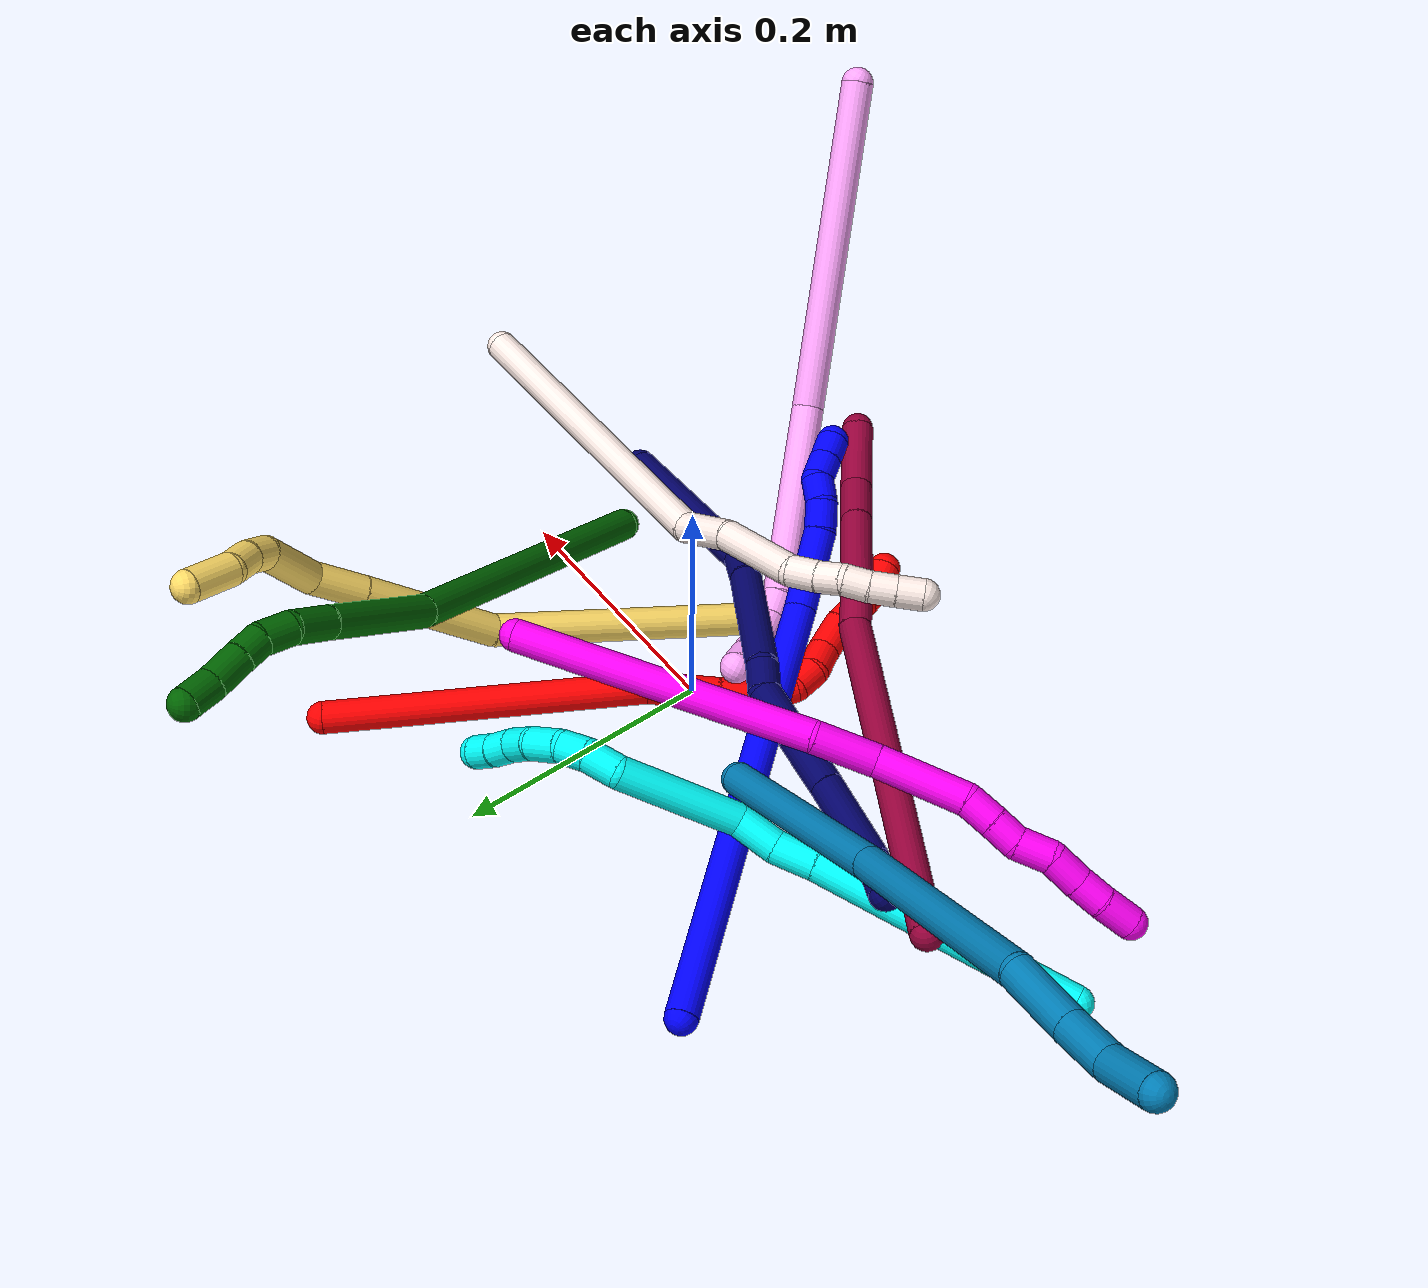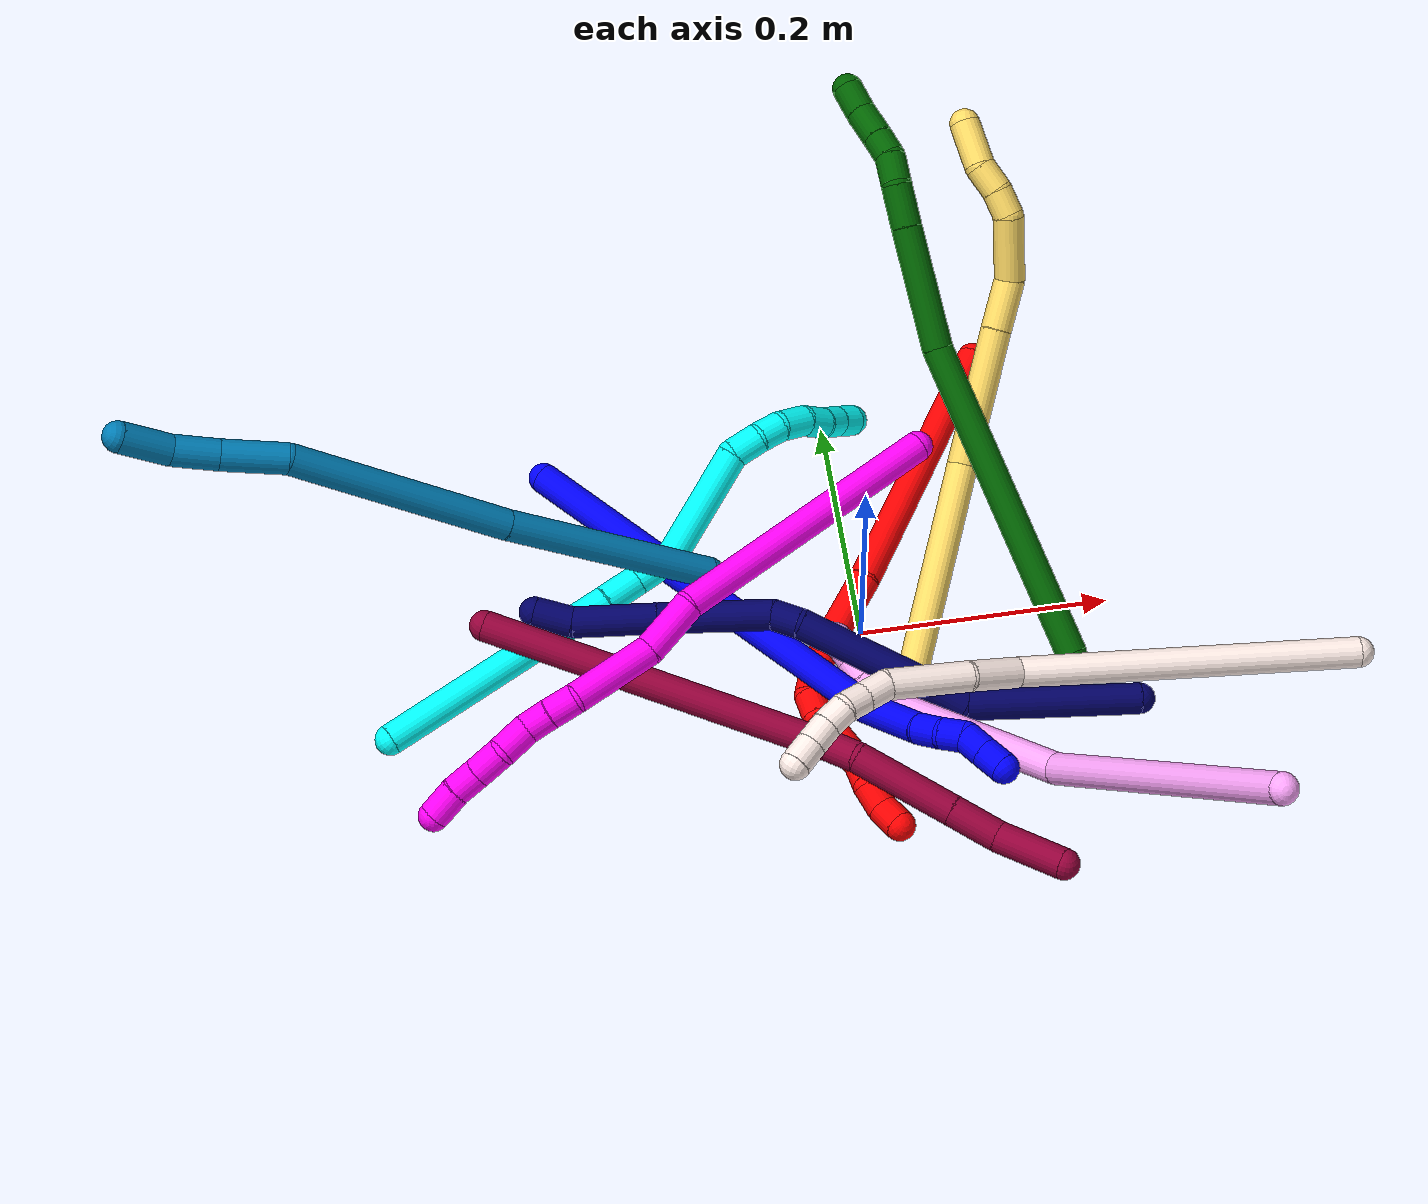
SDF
<sdf version="1.7">
 <world name="default">
  <plugin name="TubeGeneratorPlugin" filename="libtube_generator_plugin.so"/>
  <model name="photoneo_s_sensor">
   <static>1</static>
   <pose>0 0 2 1.57079 1.57079 3.14159</pose>
   <link name="link">
    <inertial><mass>0.1</mass></inertial>
    <sensor name="sensor" type="depth">
     <update_rate>30</update_rate>
     <camera>
      <horizontal_fov>1.22</horizontal_fov>
      <image><width>1920</width><height>1200</height><format>B8G8R8</format></image>
      <clip><near>0.1</near><far>4</far></clip>
      <depth_camera><output>points</output></depth_camera>
     </camera>
     <plugin name="camera_plugin" filename="libgazebo_ros_depth_camera.so">
      <baseline>0.2</baseline>
      <alwaysOn>1</alwaysOn>
      <updateRate>0.0</updateRate>
      <cameraName>camera_ir</cameraName>
      <imageTopicName>/camera/color/image_raw</imageTopicName>
      <cameraInfoTopicName>/camera/color/camera_info</cameraInfoTopicName>
      <depthImageTopicName>/camera/depth/image_raw</depthImageTopicName>
      <depthImageCameraInfoTopicName>/camera/depth/camera_info</depthImageCameraInfoTopicName>
      <pointCloudTopicName>/camera/depth/points</pointCloudTopicName>
      <frameName>fr_optical</frameName>
      <pointCloudCutoff>0.1</pointCloudCutoff>
      <pointCloudCutoffMax>2.0</pointCloudCutoffMax>
      <distortionK1>0</distortionK1>
      <distortionK2>0</distortionK2>
      <distortionK3>0</distortionK3>
      <distortionT1>0</distortionT1>
      <distortionT2>0</distortionT2>
      <CxPrime>0</CxPrime>
      <Cx>0</Cx>
      <Cy>0</Cy>
      <focalLength>0</focalLength>
      <hackBaseline>0</hackBaseline>
     </plugin>
    </sensor>
   </link>
  </model>
  <gravity>0 0 -9.8</gravity>
  <magnetic_field>6e-06 2.3e-05 -4.2e-05</magnetic_field>
  <atmosphere type="adiabatic"/>
  <physics name="default_physics" default="0" type="ode">
   <max_step_size>0.003</max_step_size>
   <real_time_factor>1</real_time_factor>
   <real_time_update_rate>1000</real_time_update_rate>
   <max_contacts>10000</max_contacts>
   <ode>
    <solver>
     <type>quick</type>
     <iters>100</iters>
     <sor>1.3</sor>
     <use_dynamic_moi_rescaling>0</use_dynamic_moi_rescaling>
    </solver>
    <constraints>
     <contact_max_correcting_vel>0</contact_max_correcting_vel>
     <contact_surface_layer>0.001</contact_surface_layer>
     <cfm>0</cfm>
     <erp>0.2</erp>
    </constraints>
   </ode>
  </physics>
  <scene><ambient>0.4 0.4 0.4 1</ambient><background>0.7 0.7 0.7 1</background><shadows>0</shadows></scene>
  <audio><device>default</device></audio>
  <spherical_coordinates>
   <surface_model>EARTH_WGS84</surface_model>
   <latitude_deg>0</latitude_deg>
   <longitude_deg>0</longitude_deg>
   <elevation>0</elevation>
   <heading_deg>0</heading_deg>
  </spherical_coordinates>
  <model name="bin">
   <static>1</static>
   <link name="bottom">
    <collision name="collision-bottom">
     <pose>0 0 -0.01 0 -0 0</pose>
     <geometry><box><size>0.8 0.6 0.02</size></box></geometry>
     <surface>
      <friction><ode><mu>100</mu><mu2>100</mu2></ode></friction>
      <contact><collide_bitmask>65535</collide_bitmask></contact>
     </surface>
    </collision>
   </link>
   <link name="west_wall">
    <collision name="collision-west_wall">
     <pose>-0.41 0 0.1 0 -0 0</pose>
     <geometry><box><size>0.02 0.6 0.2</size></box></geometry>
     <surface>
      <friction><ode><mu>100</mu><mu2>100</mu2></ode></friction>
      <contact><collide_bitmask>65535</collide_bitmask></contact>
     </surface>
    </collision>
   </link>
   <link name="east_wall">
    <collision name="collision-east_wall">
     <pose>0.41 0 0.1 0 -0 0</pose>
     <geometry><box><size>0.02 0.6 0.2</size></box></geometry>
     <surface>
      <friction><ode><mu>100</mu><mu2>100</mu2></ode></friction>
      <contact><collide_bitmask>65535</collide_bitmask></contact>
     </surface>
    </collision>
   </link>
   <link name="south_wall">
    <collision name="collision-south_wall">
     <pose>0 -0.31 0.1 0 -0 0</pose>
     <geometry><box><size>0.8 0.02 0.2</size></box></geometry>
     <surface>
      <friction><ode><mu>100</mu><mu2>100</mu2></ode></friction>
      <contact><collide_bitmask>65535</collide_bitmask></contact>
     </surface>
    </collision>
   </link>
   <link name="north_wall">
    <collision name="collision-north_wall">
     <pose>0 0.31 0.1 0 -0 0</pose>
     <geometry><box><size>0.8 0.02 0.2</size></box></geometry>
     <surface>
      <friction><ode><mu>100</mu><mu2>100</mu2></ode></friction>
      <contact><collide_bitmask>65535</collide_bitmask></contact>
     </surface>
    </collision>
   </link>
  </model>
  <model name="1">
   <static>0</static>
   <link name="1">
    <collision name="collision-cylinder-e_1_1_4">
     <pose>0.014824 -0.054235 -0.16768 2.82877 0.083921 0.520397</pose>
     <geometry><cylinder><radius>0.0125</radius><length>0.35371</length></cylinder></geometry>
     <surface>
      <friction><ode><mu>1.16</mu><mu2>1.16</mu2><slip1>0</slip1><slip2>0</slip2></ode></friction>
      <contact><ode><kp>1e+06</kp><kd>1</kd><max_vel>0</max_vel><min_depth>0.001</min_depth></ode></contact>
     </surface>
    </collision>
    <visual name="visual-cylinder-e_1_1_4">
     <pose>0.014824 -0.054235 -0.16768 2.82877 0.083921 0.520397</pose>
     <geometry><cylinder><radius>0.0125</radius><length>0.35371</length></cylinder></geometry>
     <material><ambient>0 0 1 1</ambient></material>
    </visual>
    <collision name="collision-cylinder-e_2_4_5">
     <pose>0.024348 -0.128435 -0.359529 2.45118 -0.167512 -0.458699</pose>
     <geometry><cylinder><radius>0.0125</radius><length>0.063588</length></cylinder></geometry>
     <surface>
      <friction><ode><mu>1.16</mu><mu2>1.16</mu2><slip1>0</slip1><slip2>0</slip2></ode></friction>
      <contact><ode><kp>1e+06</kp><kd>1</kd><max_vel>0</max_vel><min_depth>0.001</min_depth></ode></contact>
     </surface>
    </collision>
    <visual name="visual-cylinder-e_2_4_5">
     <pose>0.024348 -0.128435 -0.359529 2.45118 -0.167512 -0.458699</pose>
     <geometry><cylinder><radius>0.0125</radius><length>0.063588</length></cylinder></geometry>
     <material><ambient>0 0 1 1</ambient></material>
    </visual>
    <collision name="collision-cylinder-e_3_5_6">
     <pose>0.019508 -0.1559 -0.391935 2.40295 0.041344 0.106722</pose>
     <geometry><cylinder><radius>0.0125</radius><length>0.022299</length></cylinder></geometry>
     <surface>
      <friction><ode><mu>1.16</mu><mu2>1.16</mu2><slip1>0</slip1><slip2>0</slip2></ode></friction>
      <contact><ode><kp>1e+06</kp><kd>1</kd><max_vel>0</max_vel><min_depth>0.001</min_depth></ode></contact>
     </surface>
    </collision>
    <visual name="visual-cylinder-e_3_5_6">
     <pose>0.019508 -0.1559 -0.391935 2.40295 0.041344 0.106722</pose>
     <geometry><cylinder><radius>0.0125</radius><length>0.022299</length></cylinder></geometry>
     <material><ambient>0 0 1 1</ambient></material>
    </visual>
    <collision name="collision-cylinder-e_4_6_7">
     <pose>0.023092 -0.16948 -0.407487 2.44817 0.317312 0.833768</pose>
     <geometry><cylinder><radius>0.0125</radius><length>0.020023</length></cylinder></geometry>
     <surface>
      <friction><ode><mu>1.16</mu><mu2>1.16</mu2><slip1>0</slip1><slip2>0</slip2></ode></friction>
      <contact><ode><kp>1e+06</kp><kd>1</kd><max_vel>0</max_vel><min_depth>0.001</min_depth></ode></contact>
     </surface>
    </collision>
    <visual name="visual-cylinder-e_4_6_7">
     <pose>0.023092 -0.16948 -0.407487 2.44817 0.317312 0.833768</pose>
     <geometry><cylinder><radius>0.0125</radius><length>0.020023</length></cylinder></geometry>
     <material><ambient>0 0 1 1</ambient></material>
    </visual>
    <collision name="collision-cylinder-e_5_7_8">
     <pose>0.026525 -0.178197 -0.424584 2.87825 0.030437 0.228836</pose>
     <geometry><cylinder><radius>0.0125</radius><length>0.020272</length></cylinder></geometry>
     <surface>
      <friction><ode><mu>1.16</mu><mu2>1.16</mu2><slip1>0</slip1><slip2>0</slip2></ode></friction>
      <contact><ode><kp>1e+06</kp><kd>1</kd><max_vel>0</max_vel><min_depth>0.001</min_depth></ode></contact>
     </surface>
    </collision>
    <visual name="visual-cylinder-e_5_7_8">
     <pose>0.026525 -0.178197 -0.424584 2.87825 0.030437 0.228836</pose>
     <geometry><cylinder><radius>0.0125</radius><length>0.020272</length></cylinder></geometry>
     <material><ambient>0 0 1 1</ambient></material>
    </visual>
    <collision name="collision-cylinder-e_6_8_2">
     <pose>0.027129 -0.18355 -0.444042 2.86794 0.029484 0.21334</pose>
     <geometry><cylinder><radius>0.0125</radius><length>0.020108</length></cylinder></geometry>
     <surface>
      <friction><ode><mu>1.16</mu><mu2>1.16</mu2><slip1>0</slip1><slip2>0</slip2></ode></friction>
      <contact><ode><kp>1e+06</kp><kd>1</kd><max_vel>0</max_vel><min_depth>0.001</min_depth></ode></contact>
     </surface>
    </collision>
    <visual name="visual-cylinder-e_6_8_2">
     <pose>0.027129 -0.18355 -0.444042 2.86794 0.029484 0.21334</pose>
     <geometry><cylinder><radius>0.0125</radius><length>0.020108</length></cylinder></geometry>
     <material><ambient>0 0 1 1</ambient></material>
    </visual>
    <collision name="collision-sphere-2">
     <pose>0.027426 -0.186266 -0.453717 0 -0 0</pose>
     <geometry><sphere><radius>0.0125</radius></sphere></geometry>
     <surface>
      <friction><ode><mu>1.16</mu><mu2>1.16</mu2><slip1>0</slip1><slip2>0</slip2></ode></friction>
      <contact><ode><kp>1e+06</kp><kd>1</kd><max_vel>0</max_vel><min_depth>0.001</min_depth></ode></contact>
     </surface>
    </collision>
    <visual name="visual-sphere-2">
     <pose>0.027426 -0.186266 -0.453717 0 -0 0</pose>
     <geometry><sphere><radius>0.0125</radius></sphere></geometry>
     <material><ambient>0 0 1 1</ambient></material>
    </visual>
    <collision name="collision-sphere-4">
     <pose>0.029649 -0.10847 -0.335359 0 -0 0</pose>
     <geometry><sphere><radius>0.0125</radius></sphere></geometry>
     <surface>
      <friction><ode><mu>1.16</mu><mu2>1.16</mu2><slip1>0</slip1><slip2>0</slip2></ode></friction>
      <contact><ode><kp>1e+06</kp><kd>1</kd><max_vel>0</max_vel><min_depth>0.001</min_depth></ode></contact>
     </surface>
    </collision>
    <visual name="visual-sphere-4">
     <pose>0.029649 -0.10847 -0.335359 0 -0 0</pose>
     <geometry><sphere><radius>0.0125</radius></sphere></geometry>
     <material><ambient>0 0 1 1</ambient></material>
    </visual>
    <collision name="collision-sphere-1">
     <geometry><sphere><radius>0.0125</radius></sphere></geometry>
     <surface>
      <friction><ode><mu>1.16</mu><mu2>1.16</mu2><slip1>0</slip1><slip2>0</slip2></ode></friction>
      <contact><ode><kp>1e+06</kp><kd>1</kd><max_vel>0</max_vel><min_depth>0.001</min_depth></ode></contact>
     </surface>
    </collision>
    <visual name="visual-sphere-1">
     <geometry><sphere><radius>0.0125</radius></sphere></geometry>
     <material><ambient>0 0 1 1</ambient></material>
    </visual>
    <collision name="collision-sphere-8">
     <pose>0.026833 -0.180835 -0.434367 0 -0 0</pose>
     <geometry><sphere><radius>0.0125</radius></sphere></geometry>
     <surface>
      <friction><ode><mu>1.16</mu><mu2>1.16</mu2><slip1>0</slip1><slip2>0</slip2></ode></friction>
      <contact><ode><kp>1e+06</kp><kd>1</kd><max_vel>0</max_vel><min_depth>0.001</min_depth></ode></contact>
     </surface>
    </collision>
    <visual name="visual-sphere-8">
     <pose>0.026833 -0.180835 -0.434367 0 -0 0</pose>
     <geometry><sphere><radius>0.0125</radius></sphere></geometry>
     <material><ambient>0 0 1 1</ambient></material>
    </visual>
    <collision name="collision-sphere-5">
     <pose>0.019047 -0.1484 -0.383699 0 -0 0</pose>
     <geometry><sphere><radius>0.0125</radius></sphere></geometry>
     <surface>
      <friction><ode><mu>1.16</mu><mu2>1.16</mu2><slip1>0</slip1><slip2>0</slip2></ode></friction>
      <contact><ode><kp>1e+06</kp><kd>1</kd><max_vel>0</max_vel><min_depth>0.001</min_depth></ode></contact>
     </surface>
    </collision>
    <visual name="visual-sphere-5">
     <pose>0.019047 -0.1484 -0.383699 0 -0 0</pose>
     <geometry><sphere><radius>0.0125</radius></sphere></geometry>
     <material><ambient>0 0 1 1</ambient></material>
    </visual>
    <collision name="collision-sphere-6">
     <pose>0.019969 -0.1634 -0.400172 0 -0 0</pose>
     <geometry><sphere><radius>0.0125</radius></sphere></geometry>
     <surface>
      <friction><ode><mu>1.16</mu><mu2>1.16</mu2><slip1>0</slip1><slip2>0</slip2></ode></friction>
      <contact><ode><kp>1e+06</kp><kd>1</kd><max_vel>0</max_vel><min_depth>0.001</min_depth></ode></contact>
     </surface>
    </collision>
    <visual name="visual-sphere-6">
     <pose>0.019969 -0.1634 -0.400172 0 -0 0</pose>
     <geometry><sphere><radius>0.0125</radius></sphere></geometry>
     <material><ambient>0 0 1 1</ambient></material>
    </visual>
    <collision name="collision-sphere-7">
     <pose>0.026216 -0.17556 -0.414802 0 -0 0</pose>
     <geometry><sphere><radius>0.0125</radius></sphere></geometry>
     <surface>
      <friction><ode><mu>1.16</mu><mu2>1.16</mu2><slip1>0</slip1><slip2>0</slip2></ode></friction>
      <contact><ode><kp>1e+06</kp><kd>1</kd><max_vel>0</max_vel><min_depth>0.001</min_depth></ode></contact>
     </surface>
    </collision>
    <visual name="visual-sphere-7">
     <pose>0.026216 -0.17556 -0.414802 0 -0 0</pose>
     <geometry><sphere><radius>0.0125</radius></sphere></geometry>
     <material><ambient>0 0 1 1</ambient></material>
    </visual>
    <inertial>
     <pose>0.017545 -0.083047 -0.233213 0 -0 0</pose>
     <mass>0.5</mass>
     <inertia>
      <ixx>0.005055</ixx>
      <ixy>0</ixy>
      <ixz>0</ixz>
      <iyy>-0.001217</iyy>
      <iyz>0</iyz>
      <izz>0.000811</izz>
     </inertia>
    </inertial>
   </link>
   <pose>-0.233049 0.180496 0.011496 -1.40434 0.505091 0.532991</pose>
  </model>
  <model name="2">
   <static>0</static>
   <link name="2">
    <collision name="collision-cylinder-e_1_1_4">
     <pose>-0.049771 -0.109582 0.021593 1.37624 -0.419204 -0.346296</pose>
     <geometry><cylinder><radius>0.0125</radius><length>0.244553</length></cylinder></geometry>
     <surface>
      <friction><ode><mu>1.16</mu><mu2>1.16</mu2><slip1>0</slip1><slip2>0</slip2></ode></friction>
      <contact><ode><kp>1e+06</kp><kd>1</kd><max_vel>0</max_vel><min_depth>0.001</min_depth></ode></contact>
     </surface>
    </collision>
    <visual name="visual-cylinder-e_1_1_4">
     <pose>-0.049771 -0.109582 0.021593 1.37624 -0.419204 -0.346296</pose>
     <geometry><cylinder><radius>0.0125</radius><length>0.244553</length></cylinder></geometry>
     <material><ambient>1 0 0 1</ambient></material>
    </visual>
    <collision name="collision-cylinder-e_2_4_5">
     <pose>-0.111362 -0.243678 0.042972 1.57953 -0.44927 -0.453077</pose>
     <geometry><cylinder><radius>0.0125</radius><length>0.054432</length></cylinder></geometry>
     <surface>
      <friction><ode><mu>1.16</mu><mu2>1.16</mu2><slip1>0</slip1><slip2>0</slip2></ode></friction>
      <contact><ode><kp>1e+06</kp><kd>1</kd><max_vel>0</max_vel><min_depth>0.001</min_depth></ode></contact>
     </surface>
    </collision>
    <visual name="visual-cylinder-e_2_4_5">
     <pose>-0.111362 -0.243678 0.042972 1.57953 -0.44927 -0.453077</pose>
     <geometry><cylinder><radius>0.0125</radius><length>0.054432</length></cylinder></geometry>
     <material><ambient>1 0 0 1</ambient></material>
    </visual>
    <collision name="collision-cylinder-e_3_5_6">
     <pose>-0.129459 -0.282551 0.042132 1.61438 -0.411803 -0.429606</pose>
     <geometry><cylinder><radius>0.0125</radius><length>0.031366</length></cylinder></geometry>
     <surface>
      <friction><ode><mu>1.16</mu><mu2>1.16</mu2><slip1>0</slip1><slip2>0</slip2></ode></friction>
      <contact><ode><kp>1e+06</kp><kd>1</kd><max_vel>0</max_vel><min_depth>0.001</min_depth></ode></contact>
     </surface>
    </collision>
    <visual name="visual-cylinder-e_3_5_6">
     <pose>-0.129459 -0.282551 0.042132 1.61438 -0.411803 -0.429606</pose>
     <geometry><cylinder><radius>0.0125</radius><length>0.031366</length></cylinder></geometry>
     <material><ambient>1 0 0 1</ambient></material>
    </visual>
    <collision name="collision-cylinder-e_4_6_7">
     <pose>-0.138969 -0.310338 0.045884 1.25558 -0.224992 -0.163612</pose>
     <geometry><cylinder><radius>0.0125</radius><length>0.028979</length></cylinder></geometry>
     <surface>
      <friction><ode><mu>1.16</mu><mu2>1.16</mu2><slip1>0</slip1><slip2>0</slip2></ode></friction>
      <contact><ode><kp>1e+06</kp><kd>1</kd><max_vel>0</max_vel><min_depth>0.001</min_depth></ode></contact>
     </surface>
    </collision>
    <visual name="visual-cylinder-e_4_6_7">
     <pose>-0.138969 -0.310338 0.045884 1.25558 -0.224992 -0.163612</pose>
     <geometry><cylinder><radius>0.0125</radius><length>0.028979</length></cylinder></geometry>
     <material><ambient>1 0 0 1</ambient></material>
    </visual>
    <collision name="collision-cylinder-e_5_7_8">
     <pose>-0.139679 -0.33277 0.05424 1.15488 0.250876 0.163944</pose>
     <geometry><cylinder><radius>0.0125</radius><length>0.020322</length></cylinder></geometry>
     <surface>
      <friction><ode><mu>1.16</mu><mu2>1.16</mu2><slip1>0</slip1><slip2>0</slip2></ode></friction>
      <contact><ode><kp>1e+06</kp><kd>1</kd><max_vel>0</max_vel><min_depth>0.001</min_depth></ode></contact>
     </surface>
    </collision>
    <visual name="visual-cylinder-e_5_7_8">
     <pose>-0.139679 -0.33277 0.05424 1.15488 0.250876 0.163944</pose>
     <geometry><cylinder><radius>0.0125</radius><length>0.020322</length></cylinder></geometry>
     <material><ambient>1 0 0 1</ambient></material>
    </visual>
    <collision name="collision-cylinder-e_6_8_9">
     <pose>-0.129922 -0.349975 0.061914 1.14727 0.677245 0.447483</pose>
     <geometry><cylinder><radius>0.0125</radius><length>0.023088</length></cylinder></geometry>
     <surface>
      <friction><ode><mu>1.16</mu><mu2>1.16</mu2><slip1>0</slip1><slip2>0</slip2></ode></friction>
      <contact><ode><kp>1e+06</kp><kd>1</kd><max_vel>0</max_vel><min_depth>0.001</min_depth></ode></contact>
     </surface>
    </collision>
    <visual name="visual-cylinder-e_6_8_9">
     <pose>-0.129922 -0.349975 0.061914 1.14727 0.677245 0.447483</pose>
     <geometry><cylinder><radius>0.0125</radius><length>0.023088</length></cylinder></geometry>
     <material><ambient>1 0 0 1</ambient></material>
    </visual>
    <collision name="collision-cylinder-e_7_9_10">
     <pose>-0.115179 -0.369531 0.072306 1.03806 0.517813 0.300326</pose>
     <geometry><cylinder><radius>0.0125</radius><length>0.030342</length></cylinder></geometry>
     <surface>
      <friction><ode><mu>1.16</mu><mu2>1.16</mu2><slip1>0</slip1><slip2>0</slip2></ode></friction>
      <contact><ode><kp>1e+06</kp><kd>1</kd><max_vel>0</max_vel><min_depth>0.001</min_depth></ode></contact>
     </surface>
    </collision>
    <visual name="visual-cylinder-e_7_9_10">
     <pose>-0.115179 -0.369531 0.072306 1.03806 0.517813 0.300326</pose>
     <geometry><cylinder><radius>0.0125</radius><length>0.030342</length></cylinder></geometry>
     <material><ambient>1 0 0 1</ambient></material>
    </visual>
    <collision name="collision-cylinder-e_8_10_11">
     <pose>-0.105845 -0.390487 0.085406 0.98252 0.156848 0.084038</pose>
     <geometry><cylinder><radius>0.0125</radius><length>0.023368</length></cylinder></geometry>
     <surface>
      <friction><ode><mu>1.16</mu><mu2>1.16</mu2><slip1>0</slip1><slip2>0</slip2></ode></friction>
      <contact><ode><kp>1e+06</kp><kd>1</kd><max_vel>0</max_vel><min_depth>0.001</min_depth></ode></contact>
     </surface>
    </collision>
    <visual name="visual-cylinder-e_8_10_11">
     <pose>-0.105845 -0.390487 0.085406 0.98252 0.156848 0.084038</pose>
     <geometry><cylinder><radius>0.0125</radius><length>0.023368</length></cylinder></geometry>
     <material><ambient>1 0 0 1</ambient></material>
    </visual>
    <collision name="collision-cylinder-e_9_11_12">
     <pose>-0.098319 -0.409054 0.093871 1.34486 0.5547 0.445812</pose>
     <geometry><cylinder><radius>0.0125</radius><length>0.021646</length></cylinder></geometry>
     <surface>
      <friction><ode><mu>1.16</mu><mu2>1.16</mu2><slip1>0</slip1><slip2>0</slip2></ode></friction>
      <contact><ode><kp>1e+06</kp><kd>1</kd><max_vel>0</max_vel><min_depth>0.001</min_depth></ode></contact>
     </surface>
    </collision>
    <visual name="visual-cylinder-e_9_11_12">
     <pose>-0.098319 -0.409054 0.093871 1.34486 0.5547 0.445812</pose>
     <geometry><cylinder><radius>0.0125</radius><length>0.021646</length></cylinder></geometry>
     <material><ambient>1 0 0 1</ambient></material>
    </visual>
    <collision name="collision-cylinder-e_10_12_2">
     <pose>-0.087256 -0.425378 0.102019 0.879609 0.511742 0.24496</pose>
     <geometry><cylinder><radius>0.0125</radius><length>0.021904</length></cylinder></geometry>
     <surface>
      <friction><ode><mu>1.16</mu><mu2>1.16</mu2><slip1>0</slip1><slip2>0</slip2></ode></friction>
      <contact><ode><kp>1e+06</kp><kd>1</kd><max_vel>0</max_vel><min_depth>0.001</min_depth></ode></contact>
     </surface>
    </collision>
    <visual name="visual-cylinder-e_10_12_2">
     <pose>-0.087256 -0.425378 0.102019 0.879609 0.511742 0.24496</pose>
     <geometry><cylinder><radius>0.0125</radius><length>0.021904</length></cylinder></geometry>
     <material><ambient>1 0 0 1</ambient></material>
    </visual>
    <collision name="collision-sphere-2">
     <pose>-0.081893 -0.432735 0.108106 0 -0 0</pose>
     <geometry><sphere><radius>0.0125</radius></sphere></geometry>
     <surface>
      <friction><ode><mu>1.16</mu><mu2>1.16</mu2><slip1>0</slip1><slip2>0</slip2></ode></friction>
      <contact><ode><kp>1e+06</kp><kd>1</kd><max_vel>0</max_vel><min_depth>0.001</min_depth></ode></contact>
     </surface>
    </collision>
    <visual name="visual-sphere-2">
     <pose>-0.081893 -0.432735 0.108106 0 -0 0</pose>
     <geometry><sphere><radius>0.0125</radius></sphere></geometry>
     <material><ambient>1 0 0 1</ambient></material>
    </visual>
    <collision name="collision-sphere-12">
     <pose>-0.092619 -0.41802 0.095932 0 -0 0</pose>
     <geometry><sphere><radius>0.0125</radius></sphere></geometry>
     <surface>
      <friction><ode><mu>1.16</mu><mu2>1.16</mu2><slip1>0</slip1><slip2>0</slip2></ode></friction>
      <contact><ode><kp>1e+06</kp><kd>1</kd><max_vel>0</max_vel><min_depth>0.001</min_depth></ode></contact>
     </surface>
    </collision>
    <visual name="visual-sphere-12">
     <pose>-0.092619 -0.41802 0.095932 0 -0 0</pose>
     <geometry><sphere><radius>0.0125</radius></sphere></geometry>
     <material><ambient>1 0 0 1</ambient></material>
    </visual>
    <collision name="collision-sphere-11">
     <pose>-0.10402 -0.400087 0.09181 0 -0 0</pose>
     <geometry><sphere><radius>0.0125</radius></sphere></geometry>
     <surface>
      <friction><ode><mu>1.16</mu><mu2>1.16</mu2><slip1>0</slip1><slip2>0</slip2></ode></friction>
      <contact><ode><kp>1e+06</kp><kd>1</kd><max_vel>0</max_vel><min_depth>0.001</min_depth></ode></contact>
     </surface>
    </collision>
    <visual name="visual-sphere-11">
     <pose>-0.10402 -0.400087 0.09181 0 -0 0</pose>
     <geometry><sphere><radius>0.0125</radius></sphere></geometry>
     <material><ambient>1 0 0 1</ambient></material>
    </visual>
    <collision name="collision-sphere-10">
     <pose>-0.10767 -0.380886 0.079001 0 -0 0</pose>
     <geometry><sphere><radius>0.0125</radius></sphere></geometry>
     <surface>
      <friction><ode><mu>1.16</mu><mu2>1.16</mu2><slip1>0</slip1><slip2>0</slip2></ode></friction>
      <contact><ode><kp>1e+06</kp><kd>1</kd><max_vel>0</max_vel><min_depth>0.001</min_depth></ode></contact>
     </surface>
    </collision>
    <visual name="visual-sphere-10">
     <pose>-0.10767 -0.380886 0.079001 0 -0 0</pose>
     <geometry><sphere><radius>0.0125</radius></sphere></geometry>
     <material><ambient>1 0 0 1</ambient></material>
    </visual>
    <collision name="collision-sphere-9">
     <pose>-0.122688 -0.358176 0.065611 0 -0 0</pose>
     <geometry><sphere><radius>0.0125</radius></sphere></geometry>
     <surface>
      <friction><ode><mu>1.16</mu><mu2>1.16</mu2><slip1>0</slip1><slip2>0</slip2></ode></friction>
      <contact><ode><kp>1e+06</kp><kd>1</kd><max_vel>0</max_vel><min_depth>0.001</min_depth></ode></contact>
     </surface>
    </collision>
    <visual name="visual-sphere-9">
     <pose>-0.122688 -0.358176 0.065611 0 -0 0</pose>
     <geometry><sphere><radius>0.0125</radius></sphere></geometry>
     <material><ambient>1 0 0 1</ambient></material>
    </visual>
    <collision name="collision-sphere-4">
     <pose>-0.099541 -0.219164 0.043186 0 -0 0</pose>
     <geometry><sphere><radius>0.0125</radius></sphere></geometry>
     <surface>
      <friction><ode><mu>1.16</mu><mu2>1.16</mu2><slip1>0</slip1><slip2>0</slip2></ode></friction>
      <contact><ode><kp>1e+06</kp><kd>1</kd><max_vel>0</max_vel><min_depth>0.001</min_depth></ode></contact>
     </surface>
    </collision>
    <visual name="visual-sphere-4">
     <pose>-0.099541 -0.219164 0.043186 0 -0 0</pose>
     <geometry><sphere><radius>0.0125</radius></sphere></geometry>
     <material><ambient>1 0 0 1</ambient></material>
    </visual>
    <collision name="collision-sphere-1">
     <geometry><sphere><radius>0.0125</radius></sphere></geometry>
     <surface>
      <friction><ode><mu>1.16</mu><mu2>1.16</mu2><slip1>0</slip1><slip2>0</slip2></ode></friction>
      <contact><ode><kp>1e+06</kp><kd>1</kd><max_vel>0</max_vel><min_depth>0.001</min_depth></ode></contact>
     </surface>
    </collision>
    <visual name="visual-sphere-1">
     <geometry><sphere><radius>0.0125</radius></sphere></geometry>
     <material><ambient>1 0 0 1</ambient></material>
    </visual>
    <collision name="collision-sphere-8">
     <pose>-0.137156 -0.341773 0.058217 0 -0 0</pose>
     <geometry><sphere><radius>0.0125</radius></sphere></geometry>
     <surface>
      <friction><ode><mu>1.16</mu><mu2>1.16</mu2><slip1>0</slip1><slip2>0</slip2></ode></friction>
      <contact><ode><kp>1e+06</kp><kd>1</kd><max_vel>0</max_vel><min_depth>0.001</min_depth></ode></contact>
     </surface>
    </collision>
    <visual name="visual-sphere-8">
     <pose>-0.137156 -0.341773 0.058217 0 -0 0</pose>
     <geometry><sphere><radius>0.0125</radius></sphere></geometry>
     <material><ambient>1 0 0 1</ambient></material>
    </visual>
    <collision name="collision-sphere-5">
     <pose>-0.123182 -0.268193 0.042758 0 -0 0</pose>
     <geometry><sphere><radius>0.0125</radius></sphere></geometry>
     <surface>
      <friction><ode><mu>1.16</mu><mu2>1.16</mu2><slip1>0</slip1><slip2>0</slip2></ode></friction>
      <contact><ode><kp>1e+06</kp><kd>1</kd><max_vel>0</max_vel><min_depth>0.001</min_depth></ode></contact>
     </surface>
    </collision>
    <visual name="visual-sphere-5">
     <pose>-0.123182 -0.268193 0.042758 0 -0 0</pose>
     <geometry><sphere><radius>0.0125</radius></sphere></geometry>
     <material><ambient>1 0 0 1</ambient></material>
    </visual>
    <collision name="collision-sphere-6">
     <pose>-0.135736 -0.296909 0.041506 0 -0 0</pose>
     <geometry><sphere><radius>0.0125</radius></sphere></geometry>
     <surface>
      <friction><ode><mu>1.16</mu><mu2>1.16</mu2><slip1>0</slip1><slip2>0</slip2></ode></friction>
      <contact><ode><kp>1e+06</kp><kd>1</kd><max_vel>0</max_vel><min_depth>0.001</min_depth></ode></contact>
     </surface>
    </collision>
    <visual name="visual-sphere-6">
     <pose>-0.135736 -0.296909 0.041506 0 -0 0</pose>
     <geometry><sphere><radius>0.0125</radius></sphere></geometry>
     <material><ambient>1 0 0 1</ambient></material>
    </visual>
    <collision name="collision-sphere-7">
     <pose>-0.142201 -0.323766 0.050263 0 -0 0</pose>
     <geometry><sphere><radius>0.0125</radius></sphere></geometry>
     <surface>
      <friction><ode><mu>1.16</mu><mu2>1.16</mu2><slip1>0</slip1><slip2>0</slip2></ode></friction>
      <contact><ode><kp>1e+06</kp><kd>1</kd><max_vel>0</max_vel><min_depth>0.001</min_depth></ode></contact>
     </surface>
    </collision>
    <visual name="visual-sphere-7">
     <pose>-0.142201 -0.323766 0.050263 0 -0 0</pose>
     <geometry><sphere><radius>0.0125</radius></sphere></geometry>
     <material><ambient>1 0 0 1</ambient></material>
    </visual>
    <inertial>
     <pose>-0.084334 -0.22254 0.042518 0 -0 0</pose>
     <mass>0.5</mass>
     <inertia>
      <ixx>0.000692</ixx>
      <ixy>0</ixy>
      <ixz>0</ixz>
      <iyy>-1.8e-05</iyy>
      <iyz>0</iyz>
      <izz>0.001643</izz>
     </inertia>
    </inertial>
   </link>
   <pose>0.134981 0.244804 0.01251 0.298149 0.329727 -0.116699</pose>
  </model>
  <model name="3">
   <static>0</static>
   <link name="3">
    <collision name="collision-cylinder-e_1_1_4">
     <pose>0.00408 0.090204 -0.047245 -2.05327 0.04005 -0.066172</pose>
     <geometry><cylinder><radius>0.0125</radius><length>0.203819</length></cylinder></geometry>
     <surface>
      <friction><ode><mu>1.16</mu><mu2>1.16</mu2><slip1>0</slip1><slip2>0</slip2></ode></friction>
      <contact><ode><kp>1e+06</kp><kd>1</kd><max_vel>0</max_vel><min_depth>0.001</min_depth></ode></contact>
     </surface>
    </collision>
    <visual name="visual-cylinder-e_1_1_4">
     <pose>0.00408 0.090204 -0.047245 -2.05327 0.04005 -0.066172</pose>
     <geometry><cylinder><radius>0.0125</radius><length>0.203819</length></cylinder></geometry>
     <material><ambient>0.003922 1 0.996078 1</ambient></material>
    </visual>
    <collision name="collision-cylinder-e_2_4_5">
     <pose>0.008911 0.195031 -0.100556 -1.96407 0.047352 -0.070895</pose>
     <geometry><cylinder><radius>0.0125</radius><length>0.031698</length></cylinder></geometry>
     <surface>
      <friction><ode><mu>1.16</mu><mu2>1.16</mu2><slip1>0</slip1><slip2>0</slip2></ode></friction>
      <contact><ode><kp>1e+06</kp><kd>1</kd><max_vel>0</max_vel><min_depth>0.001</min_depth></ode></contact>
     </surface>
    </collision>
    <visual name="visual-cylinder-e_2_4_5">
     <pose>0.008911 0.195031 -0.100556 -1.96407 0.047352 -0.070895</pose>
     <geometry><cylinder><radius>0.0125</radius><length>0.031698</length></cylinder></geometry>
     <material><ambient>0.003922 1 0.996078 1</ambient></material>
    </visual>
    <collision name="collision-cylinder-e_3_5_6">
     <pose>0.01068 0.222572 -0.116667 -2.23167 0.062196 -0.127011</pose>
     <geometry><cylinder><radius>0.0125</radius><length>0.032791</length></cylinder></geometry>
     <surface>
      <friction><ode><mu>1.16</mu><mu2>1.16</mu2><slip1>0</slip1><slip2>0</slip2></ode></friction>
      <contact><ode><kp>1e+06</kp><kd>1</kd><max_vel>0</max_vel><min_depth>0.001</min_depth></ode></contact>
     </surface>
    </collision>
    <visual name="visual-cylinder-e_3_5_6">
     <pose>0.01068 0.222572 -0.116667 -2.23167 0.062196 -0.127011</pose>
     <geometry><cylinder><radius>0.0125</radius><length>0.032791</length></cylinder></geometry>
     <material><ambient>0.003922 1 0.996078 1</ambient></material>
    </visual>
    <collision name="collision-cylinder-e_4_6_7">
     <pose>0.034624 0.269358 -0.15152 -2.20301 0.499811 -0.932666</pose>
     <geometry><cylinder><radius>0.0125</radius><length>0.095667</length></cylinder></geometry>
     <surface>
      <friction><ode><mu>1.16</mu><mu2>1.16</mu2><slip1>0</slip1><slip2>0</slip2></ode></friction>
      <contact><ode><kp>1e+06</kp><kd>1</kd><max_vel>0</max_vel><min_depth>0.001</min_depth></ode></contact>
     </surface>
    </collision>
    <visual name="visual-cylinder-e_4_6_7">
     <pose>0.034624 0.269358 -0.15152 -2.20301 0.499811 -0.932666</pose>
     <geometry><cylinder><radius>0.0125</radius><length>0.095667</length></cylinder></geometry>
     <material><ambient>0.003922 1 0.996078 1</ambient></material>
    </visual>
    <collision name="collision-cylinder-e_5_7_8">
     <pose>0.058036 0.314119 -0.18237 -2.07717 0.039111 -0.066399</pose>
     <geometry><cylinder><radius>0.0125</radius><length>0.024933</length></cylinder></geometry>
     <surface>
      <friction><ode><mu>1.16</mu><mu2>1.16</mu2><slip1>0</slip1><slip2>0</slip2></ode></friction>
      <contact><ode><kp>1e+06</kp><kd>1</kd><max_vel>0</max_vel><min_depth>0.001</min_depth></ode></contact>
     </surface>
    </collision>
    <visual name="visual-cylinder-e_5_7_8">
     <pose>0.058036 0.314119 -0.18237 -2.07717 0.039111 -0.066399</pose>
     <geometry><cylinder><radius>0.0125</radius><length>0.024933</length></cylinder></geometry>
     <material><ambient>0.003922 1 0.996078 1</ambient></material>
    </visual>
    <collision name="collision-cylinder-e_6_8_9">
     <pose>0.05819 0.335218 -0.191079 -1.82644 -0.031605 0.040925</pose>
     <geometry><cylinder><radius>0.0125</radius><length>0.021106</length></cylinder></geometry>
     <surface>
      <friction><ode><mu>1.16</mu><mu2>1.16</mu2><slip1>0</slip1><slip2>0</slip2></ode></friction>
      <contact><ode><kp>1e+06</kp><kd>1</kd><max_vel>0</max_vel><min_depth>0.001</min_depth></ode></contact>
     </surface>
    </collision>
    <visual name="visual-cylinder-e_6_8_9">
     <pose>0.05819 0.335218 -0.191079 -1.82644 -0.031605 0.040925</pose>
     <geometry><cylinder><radius>0.0125</radius><length>0.021106</length></cylinder></geometry>
     <material><ambient>0.003922 1 0.996078 1</ambient></material>
    </visual>
    <collision name="collision-cylinder-e_7_9_10">
     <pose>0.055041 0.35841 -0.193282 -1.53502 -0.213325 0.205881</pose>
     <geometry><cylinder><radius>0.0125</radius><length>0.026594</length></cylinder></geometry>
     <surface>
      <friction><ode><mu>1.16</mu><mu2>1.16</mu2><slip1>0</slip1><slip2>0</slip2></ode></friction>
      <contact><ode><kp>1e+06</kp><kd>1</kd><max_vel>0</max_vel><min_depth>0.001</min_depth></ode></contact>
     </surface>
    </collision>
    <visual name="visual-cylinder-e_7_9_10">
     <pose>0.055041 0.35841 -0.193282 -1.53502 -0.213325 0.205881</pose>
     <geometry><cylinder><radius>0.0125</radius><length>0.026594</length></cylinder></geometry>
     <material><ambient>0.003922 1 0.996078 1</ambient></material>
    </visual>
    <collision name="collision-cylinder-e_8_10_11">
     <pose>0.047536 0.381581 -0.190262 -1.32496 -0.420095 0.329601</pose>
     <geometry><cylinder><radius>0.0125</radius><length>0.022998</length></cylinder></geometry>
     <surface>
      <friction><ode><mu>1.16</mu><mu2>1.16</mu2><slip1>0</slip1><slip2>0</slip2></ode></friction>
      <contact><ode><kp>1e+06</kp><kd>1</kd><max_vel>0</max_vel><min_depth>0.001</min_depth></ode></contact>
     </surface>
    </collision>
    <visual name="visual-cylinder-e_8_10_11">
     <pose>0.047536 0.381581 -0.190262 -1.32496 -0.420095 0.329601</pose>
     <geometry><cylinder><radius>0.0125</radius><length>0.022998</length></cylinder></geometry>
     <material><ambient>0.003922 1 0.996078 1</ambient></material>
    </visual>
    <collision name="collision-cylinder-e_9_11_12">
     <pose>0.040716 0.401118 -0.184562 -1.24642 -0.212684 0.15315</pose>
     <geometry><cylinder><radius>0.0125</radius><length>0.02019</length></cylinder></geometry>
     <surface>
      <friction><ode><mu>1.16</mu><mu2>1.16</mu2><slip1>0</slip1><slip2>0</slip2></ode></friction>
      <contact><ode><kp>1e+06</kp><kd>1</kd><max_vel>0</max_vel><min_depth>0.001</min_depth></ode></contact>
     </surface>
    </collision>
    <visual name="visual-cylinder-e_9_11_12">
     <pose>0.040716 0.401118 -0.184562 -1.24642 -0.212684 0.15315</pose>
     <geometry><cylinder><radius>0.0125</radius><length>0.02019</length></cylinder></geometry>
     <material><ambient>0.003922 1 0.996078 1</ambient></material>
    </visual>
    <collision name="collision-cylinder-e_10_12_2">
     <pose>0.035695 0.4199 -0.179226 -1.34248 -0.290141 0.23105</pose>
     <geometry><cylinder><radius>0.0125</radius><length>0.020205</length></cylinder></geometry>
     <surface>
      <friction><ode><mu>1.16</mu><mu2>1.16</mu2><slip1>0</slip1><slip2>0</slip2></ode></friction>
      <contact><ode><kp>1e+06</kp><kd>1</kd><max_vel>0</max_vel><min_depth>0.001</min_depth></ode></contact>
     </surface>
    </collision>
    <visual name="visual-cylinder-e_10_12_2">
     <pose>0.035695 0.4199 -0.179226 -1.34248 -0.290141 0.23105</pose>
     <geometry><cylinder><radius>0.0125</radius><length>0.020205</length></cylinder></geometry>
     <material><ambient>0.003922 1 0.996078 1</ambient></material>
    </visual>
    <collision name="collision-sphere-2">
     <pose>0.032804 0.429329 -0.177035 0 -0 0</pose>
     <geometry><sphere><radius>0.0125</radius></sphere></geometry>
     <surface>
      <friction><ode><mu>1.16</mu><mu2>1.16</mu2><slip1>0</slip1><slip2>0</slip2></ode></friction>
      <contact><ode><kp>1e+06</kp><kd>1</kd><max_vel>0</max_vel><min_depth>0.001</min_depth></ode></contact>
     </surface>
    </collision>
    <visual name="visual-sphere-2">
     <pose>0.032804 0.429329 -0.177035 0 -0 0</pose>
     <geometry><sphere><radius>0.0125</radius></sphere></geometry>
     <material><ambient>0.003922 1 0.996078 1</ambient></material>
    </visual>
    <collision name="collision-sphere-12">
     <pose>0.038585 0.410471 -0.181417 0 -0 0</pose>
     <geometry><sphere><radius>0.0125</radius></sphere></geometry>
     <surface>
      <friction><ode><mu>1.16</mu><mu2>1.16</mu2><slip1>0</slip1><slip2>0</slip2></ode></friction>
      <contact><ode><kp>1e+06</kp><kd>1</kd><max_vel>0</max_vel><min_depth>0.001</min_depth></ode></contact>
     </surface>
    </collision>
    <visual name="visual-sphere-12">
     <pose>0.038585 0.410471 -0.181417 0 -0 0</pose>
     <geometry><sphere><radius>0.0125</radius></sphere></geometry>
     <material><ambient>0.003922 1 0.996078 1</ambient></material>
    </visual>
    <collision name="collision-sphere-11">
     <pose>0.042847 0.391765 -0.187707 0 -0 0</pose>
     <geometry><sphere><radius>0.0125</radius></sphere></geometry>
     <surface>
      <friction><ode><mu>1.16</mu><mu2>1.16</mu2><slip1>0</slip1><slip2>0</slip2></ode></friction>
      <contact><ode><kp>1e+06</kp><kd>1</kd><max_vel>0</max_vel><min_depth>0.001</min_depth></ode></contact>
     </surface>
    </collision>
    <visual name="visual-sphere-11">
     <pose>0.042847 0.391765 -0.187707 0 -0 0</pose>
     <geometry><sphere><radius>0.0125</radius></sphere></geometry>
     <material><ambient>0.003922 1 0.996078 1</ambient></material>
    </visual>
    <collision name="collision-sphere-10">
     <pose>0.052226 0.371398 -0.192817 0 -0 0</pose>
     <geometry><sphere><radius>0.0125</radius></sphere></geometry>
     <surface>
      <friction><ode><mu>1.16</mu><mu2>1.16</mu2><slip1>0</slip1><slip2>0</slip2></ode></friction>
      <contact><ode><kp>1e+06</kp><kd>1</kd><max_vel>0</max_vel><min_depth>0.001</min_depth></ode></contact>
     </surface>
    </collision>
    <visual name="visual-sphere-10">
     <pose>0.052226 0.371398 -0.192817 0 -0 0</pose>
     <geometry><sphere><radius>0.0125</radius></sphere></geometry>
     <material><ambient>0.003922 1 0.996078 1</ambient></material>
    </visual>
    <collision name="collision-sphere-9">
     <pose>0.057857 0.345423 -0.193746 0 -0 0</pose>
     <geometry><sphere><radius>0.0125</radius></sphere></geometry>
     <surface>
      <friction><ode><mu>1.16</mu><mu2>1.16</mu2><slip1>0</slip1><slip2>0</slip2></ode></friction>
      <contact><ode><kp>1e+06</kp><kd>1</kd><max_vel>0</max_vel><min_depth>0.001</min_depth></ode></contact>
     </surface>
    </collision>
    <visual name="visual-sphere-9">
     <pose>0.057857 0.345423 -0.193746 0 -0 0</pose>
     <geometry><sphere><radius>0.0125</radius></sphere></geometry>
     <material><ambient>0.003922 1 0.996078 1</ambient></material>
    </visual>
    <collision name="collision-sphere-4">
     <pose>0.008161 0.180408 -0.09449 0 -0 0</pose>
     <geometry><sphere><radius>0.0125</radius></sphere></geometry>
     <surface>
      <friction><ode><mu>1.16</mu><mu2>1.16</mu2><slip1>0</slip1><slip2>0</slip2></ode></friction>
      <contact><ode><kp>1e+06</kp><kd>1</kd><max_vel>0</max_vel><min_depth>0.001</min_depth></ode></contact>
     </surface>
    </collision>
    <visual name="visual-sphere-4">
     <pose>0.008161 0.180408 -0.09449 0 -0 0</pose>
     <geometry><sphere><radius>0.0125</radius></sphere></geometry>
     <material><ambient>0.003922 1 0.996078 1</ambient></material>
    </visual>
    <collision name="collision-sphere-1">
     <geometry><sphere><radius>0.0125</radius></sphere></geometry>
     <surface>
      <friction><ode><mu>1.16</mu><mu2>1.16</mu2><slip1>0</slip1><slip2>0</slip2></ode></friction>
      <contact><ode><kp>1e+06</kp><kd>1</kd><max_vel>0</max_vel><min_depth>0.001</min_depth></ode></contact>
     </surface>
    </collision>
    <visual name="visual-sphere-1">
     <geometry><sphere><radius>0.0125</radius></sphere></geometry>
     <material><ambient>0.003922 1 0.996078 1</ambient></material>
    </visual>
    <collision name="collision-sphere-8">
     <pose>0.058523 0.325013 -0.188412 0 -0 0</pose>
     <geometry><sphere><radius>0.0125</radius></sphere></geometry>
     <surface>
      <friction><ode><mu>1.16</mu><mu2>1.16</mu2><slip1>0</slip1><slip2>0</slip2></ode></friction>
      <contact><ode><kp>1e+06</kp><kd>1</kd><max_vel>0</max_vel><min_depth>0.001</min_depth></ode></contact>
     </surface>
    </collision>
    <visual name="visual-sphere-8">
     <pose>0.058523 0.325013 -0.188412 0 -0 0</pose>
     <geometry><sphere><radius>0.0125</radius></sphere></geometry>
     <material><ambient>0.003922 1 0.996078 1</ambient></material>
    </visual>
    <collision name="collision-sphere-5">
     <pose>0.009661 0.209653 -0.106623 0 -0 0</pose>
     <geometry><sphere><radius>0.0125</radius></sphere></geometry>
     <surface>
      <friction><ode><mu>1.16</mu><mu2>1.16</mu2><slip1>0</slip1><slip2>0</slip2></ode></friction>
      <contact><ode><kp>1e+06</kp><kd>1</kd><max_vel>0</max_vel><min_depth>0.001</min_depth></ode></contact>
     </surface>
    </collision>
    <visual name="visual-sphere-5">
     <pose>0.009661 0.209653 -0.106623 0 -0 0</pose>
     <geometry><sphere><radius>0.0125</radius></sphere></geometry>
     <material><ambient>0.003922 1 0.996078 1</ambient></material>
    </visual>
    <collision name="collision-sphere-6">
     <pose>0.011699 0.23549 -0.126711 0 -0 0</pose>
     <geometry><sphere><radius>0.0125</radius></sphere></geometry>
     <surface>
      <friction><ode><mu>1.16</mu><mu2>1.16</mu2><slip1>0</slip1><slip2>0</slip2></ode></friction>
      <contact><ode><kp>1e+06</kp><kd>1</kd><max_vel>0</max_vel><min_depth>0.001</min_depth></ode></contact>
     </surface>
    </collision>
    <visual name="visual-sphere-6">
     <pose>0.011699 0.23549 -0.126711 0 -0 0</pose>
     <geometry><sphere><radius>0.0125</radius></sphere></geometry>
     <material><ambient>0.003922 1 0.996078 1</ambient></material>
    </visual>
    <collision name="collision-sphere-7">
     <pose>0.057549 0.303226 -0.176329 0 -0 0</pose>
     <geometry><sphere><radius>0.0125</radius></sphere></geometry>
     <surface>
      <friction><ode><mu>1.16</mu><mu2>1.16</mu2><slip1>0</slip1><slip2>0</slip2></ode></friction>
      <contact><ode><kp>1e+06</kp><kd>1</kd><max_vel>0</max_vel><min_depth>0.001</min_depth></ode></contact>
     </surface>
    </collision>
    <visual name="visual-sphere-7">
     <pose>0.057549 0.303226 -0.176329 0 -0 0</pose>
     <geometry><sphere><radius>0.0125</radius></sphere></geometry>
     <material><ambient>0.003922 1 0.996078 1</ambient></material>
    </visual>
    <inertial>
     <pose>0.023104 0.214862 -0.113162 0 -0 0</pose>
     <mass>0.5</mass>
     <inertia>
      <ixx>0.000672</ixx>
      <ixy>0</ixy>
      <ixz>0</ixz>
      <iyy>-0.000402</iyy>
      <iyz>0</iyz>
      <izz>-0.000781</izz>
     </inertia>
    </inertial>
   </link>
   <pose>-0.384216 -0.047072 0.011496 -2.78153 -0.50015 2.03245</pose>
  </model>
  <model name="4">
   <static>0</static>
   <link name="4">
    <collision name="collision-cylinder-e_1_1_4">
     <pose>-0.043225 0.025258 -0.119558 -2.93339 -0.339998 2.04807</pose>
     <geometry><cylinder><radius>0.0125</radius><length>0.259233</length></cylinder></geometry>
     <surface>
      <friction><ode><mu>1.16</mu><mu2>1.16</mu2><slip1>0</slip1><slip2>0</slip2></ode></friction>
      <contact><ode><kp>1e+06</kp><kd>1</kd><max_vel>0</max_vel><min_depth>0.001</min_depth></ode></contact>
     </surface>
    </collision>
    <visual name="visual-cylinder-e_1_1_4">
     <pose>-0.043225 0.025258 -0.119558 -2.93339 -0.339998 2.04807</pose>
     <geometry><cylinder><radius>0.0125</radius><length>0.259233</length></cylinder></geometry>
     <material><ambient>1 0.65098 0.996078 1</ambient></material>
    </visual>
    <collision name="collision-cylinder-e_2_4_5">
     <pose>-0.110018 0.093093 -0.300253 -2.53328 -0.306372 0.914249</pose>
     <geometry><cylinder><radius>0.0125</radius><length>0.156281</length></cylinder></geometry>
     <surface>
      <friction><ode><mu>1.16</mu><mu2>1.16</mu2><slip1>0</slip1><slip2>0</slip2></ode></friction>
      <contact><ode><kp>1e+06</kp><kd>1</kd><max_vel>0</max_vel><min_depth>0.001</min_depth></ode></contact>
     </surface>
    </collision>
    <visual name="visual-cylinder-e_2_4_5">
     <pose>-0.110018 0.093093 -0.300253 -2.53328 -0.306372 0.914249</pose>
     <geometry><cylinder><radius>0.0125</radius><length>0.156281</length></cylinder></geometry>
     <material><ambient>1 0.65098 0.996078 1</ambient></material>
    </visual>
    <collision name="collision-cylinder-e_3_5_6">
     <pose>-0.134772 0.14065 -0.370079 -2.62107 -0.117951 0.436375</pose>
     <geometry><cylinder><radius>0.0125</radius><length>0.02017</length></cylinder></geometry>
     <surface>
      <friction><ode><mu>1.16</mu><mu2>1.16</mu2><slip1>0</slip1><slip2>0</slip2></ode></friction>
      <contact><ode><kp>1e+06</kp><kd>1</kd><max_vel>0</max_vel><min_depth>0.001</min_depth></ode></contact>
     </surface>
    </collision>
    <visual name="visual-cylinder-e_3_5_6">
     <pose>-0.134772 0.14065 -0.370079 -2.62107 -0.117951 0.436375</pose>
     <geometry><cylinder><radius>0.0125</radius><length>0.02017</length></cylinder></geometry>
     <material><ambient>1 0.65098 0.996078 1</ambient></material>
    </visual>
    <collision name="collision-cylinder-e_4_6_7">
     <pose>-0.136286 0.154871 -0.385651 -2.21098 -0.02836 0.056475</pose>
     <geometry><cylinder><radius>0.0125</radius><length>0.023053</length></cylinder></geometry>
     <surface>
      <friction><ode><mu>1.16</mu><mu2>1.16</mu2><slip1>0</slip1><slip2>0</slip2></ode></friction>
      <contact><ode><kp>1e+06</kp><kd>1</kd><max_vel>0</max_vel><min_depth>0.001</min_depth></ode></contact>
     </surface>
    </collision>
    <visual name="visual-cylinder-e_4_6_7">
     <pose>-0.136286 0.154871 -0.385651 -2.21098 -0.02836 0.056475</pose>
     <geometry><cylinder><radius>0.0125</radius><length>0.023053</length></cylinder></geometry>
     <material><ambient>1 0.65098 0.996078 1</ambient></material>
    </visual>
    <collision name="collision-cylinder-e_5_7_8">
     <pose>-0.134609 0.1719 -0.398523 -2.22642 0.201114 -0.404186</pose>
     <geometry><cylinder><radius>0.0125</radius><length>0.020055</length></cylinder></geometry>
     <surface>
      <friction><ode><mu>1.16</mu><mu2>1.16</mu2><slip1>0</slip1><slip2>0</slip2></ode></friction>
      <contact><ode><kp>1e+06</kp><kd>1</kd><max_vel>0</max_vel><min_depth>0.001</min_depth></ode></contact>
     </surface>
    </collision>
    <visual name="visual-cylinder-e_5_7_8">
     <pose>-0.134609 0.1719 -0.398523 -2.22642 0.201114 -0.404186</pose>
     <geometry><cylinder><radius>0.0125</radius><length>0.020055</length></cylinder></geometry>
     <material><ambient>1 0.65098 0.996078 1</ambient></material>
    </visual>
    <collision name="collision-cylinder-e_6_8_2">
     <pose>-0.131169 0.189663 -0.40781 -1.88997 0.135969 -0.18787</pose>
     <geometry><cylinder><radius>0.0125</radius><length>0.021207</length></cylinder></geometry>
     <surface>
      <friction><ode><mu>1.16</mu><mu2>1.16</mu2><slip1>0</slip1><slip2>0</slip2></ode></friction>
      <contact><ode><kp>1e+06</kp><kd>1</kd><max_vel>0</max_vel><min_depth>0.001</min_depth></ode></contact>
     </surface>
    </collision>
    <visual name="visual-cylinder-e_6_8_2">
     <pose>-0.131169 0.189663 -0.40781 -1.88997 0.135969 -0.18787</pose>
     <geometry><cylinder><radius>0.0125</radius><length>0.021207</length></cylinder></geometry>
     <material><ambient>1 0.65098 0.996078 1</ambient></material>
    </visual>
    <collision name="collision-sphere-2">
     <pose>-0.129732 0.199638 -0.411106 0 -0 0</pose>
     <geometry><sphere><radius>0.0125</radius></sphere></geometry>
     <surface>
      <friction><ode><mu>1.16</mu><mu2>1.16</mu2><slip1>0</slip1><slip2>0</slip2></ode></friction>
      <contact><ode><kp>1e+06</kp><kd>1</kd><max_vel>0</max_vel><min_depth>0.001</min_depth></ode></contact>
     </surface>
    </collision>
    <visual name="visual-sphere-2">
     <pose>-0.129732 0.199638 -0.411106 0 -0 0</pose>
     <geometry><sphere><radius>0.0125</radius></sphere></geometry>
     <material><ambient>1 0.65098 0.996078 1</ambient></material>
    </visual>
    <collision name="collision-sphere-4">
     <pose>-0.08645 0.050517 -0.239116 0 -0 0</pose>
     <geometry><sphere><radius>0.0125</radius></sphere></geometry>
     <surface>
      <friction><ode><mu>1.16</mu><mu2>1.16</mu2><slip1>0</slip1><slip2>0</slip2></ode></friction>
      <contact><ode><kp>1e+06</kp><kd>1</kd><max_vel>0</max_vel><min_depth>0.001</min_depth></ode></contact>
     </surface>
    </collision>
    <visual name="visual-sphere-4">
     <pose>-0.08645 0.050517 -0.239116 0 -0 0</pose>
     <geometry><sphere><radius>0.0125</radius></sphere></geometry>
     <material><ambient>1 0.65098 0.996078 1</ambient></material>
    </visual>
    <collision name="collision-sphere-1">
     <geometry><sphere><radius>0.0125</radius></sphere></geometry>
     <surface>
      <friction><ode><mu>1.16</mu><mu2>1.16</mu2><slip1>0</slip1><slip2>0</slip2></ode></friction>
      <contact><ode><kp>1e+06</kp><kd>1</kd><max_vel>0</max_vel><min_depth>0.001</min_depth></ode></contact>
     </surface>
    </collision>
    <visual name="visual-sphere-1">
     <geometry><sphere><radius>0.0125</radius></sphere></geometry>
     <material><ambient>1 0.65098 0.996078 1</ambient></material>
    </visual>
    <collision name="collision-sphere-8">
     <pose>-0.132606 0.179688 -0.404513 0 -0 0</pose>
     <geometry><sphere><radius>0.0125</radius></sphere></geometry>
     <surface>
      <friction><ode><mu>1.16</mu><mu2>1.16</mu2><slip1>0</slip1><slip2>0</slip2></ode></friction>
      <contact><ode><kp>1e+06</kp><kd>1</kd><max_vel>0</max_vel><min_depth>0.001</min_depth></ode></contact>
     </surface>
    </collision>
    <visual name="visual-sphere-8">
     <pose>-0.132606 0.179688 -0.404513 0 -0 0</pose>
     <geometry><sphere><radius>0.0125</radius></sphere></geometry>
     <material><ambient>1 0.65098 0.996078 1</ambient></material>
    </visual>
    <collision name="collision-sphere-5">
     <pose>-0.133585 0.135669 -0.361391 0 -0 0</pose>
     <geometry><sphere><radius>0.0125</radius></sphere></geometry>
     <surface>
      <friction><ode><mu>1.16</mu><mu2>1.16</mu2><slip1>0</slip1><slip2>0</slip2></ode></friction>
      <contact><ode><kp>1e+06</kp><kd>1</kd><max_vel>0</max_vel><min_depth>0.001</min_depth></ode></contact>
     </surface>
    </collision>
    <visual name="visual-sphere-5">
     <pose>-0.133585 0.135669 -0.361391 0 -0 0</pose>
     <geometry><sphere><radius>0.0125</radius></sphere></geometry>
     <material><ambient>1 0.65098 0.996078 1</ambient></material>
    </visual>
    <collision name="collision-sphere-6">
     <pose>-0.135959 0.145631 -0.378768 0 -0 0</pose>
     <geometry><sphere><radius>0.0125</radius></sphere></geometry>
     <surface>
      <friction><ode><mu>1.16</mu><mu2>1.16</mu2><slip1>0</slip1><slip2>0</slip2></ode></friction>
      <contact><ode><kp>1e+06</kp><kd>1</kd><max_vel>0</max_vel><min_depth>0.001</min_depth></ode></contact>
     </surface>
    </collision>
    <visual name="visual-sphere-6">
     <pose>-0.135959 0.145631 -0.378768 0 -0 0</pose>
     <geometry><sphere><radius>0.0125</radius></sphere></geometry>
     <material><ambient>1 0.65098 0.996078 1</ambient></material>
    </visual>
    <collision name="collision-sphere-7">
     <pose>-0.136612 0.164112 -0.392533 0 -0 0</pose>
     <geometry><sphere><radius>0.0125</radius></sphere></geometry>
     <surface>
      <friction><ode><mu>1.16</mu><mu2>1.16</mu2><slip1>0</slip1><slip2>0</slip2></ode></friction>
      <contact><ode><kp>1e+06</kp><kd>1</kd><max_vel>0</max_vel><min_depth>0.001</min_depth></ode></contact>
     </surface>
    </collision>
    <visual name="visual-sphere-7">
     <pose>-0.136612 0.164112 -0.392533 0 -0 0</pose>
     <geometry><sphere><radius>0.0125</radius></sphere></geometry>
     <material><ambient>1 0.65098 0.996078 1</ambient></material>
    </visual>
    <inertial>
     <pose>-0.079481 0.069947 -0.221826 0 -0 0</pose>
     <mass>0.5</mass>
     <inertia><ixx>0.00102</ixx><ixy>0</ixy><ixz>0</ixz><iyy>0.002109</iyy><iyz>0</iyz><izz>8.6e-05</izz></inertia>
    </inertial>
   </link>
   <pose>0.242839 -0.339755 0.269644 0.658021 -0.306985 0.551234</pose>
  </model>
  <model name="5">
   <static>0</static>
   <link name="5">
    <collision name="collision-cylinder-e_1_1_4">
     <pose>-0.014872 0.02398 0.099134 -0.237331 -0.144793 0.017293</pose>
     <geometry><cylinder><radius>0.0125</radius><length>0.206144</length></cylinder></geometry>
     <surface>
      <friction><ode><mu>1.16</mu><mu2>1.16</mu2><slip1>0</slip1><slip2>0</slip2></ode></friction>
      <contact><ode><kp>1e+06</kp><kd>1</kd><max_vel>0</max_vel><min_depth>0.001</min_depth></ode></contact>
     </surface>
    </collision>
    <visual name="visual-cylinder-e_1_1_4">
     <pose>-0.014872 0.02398 0.099134 -0.237331 -0.144793 0.017293</pose>
     <geometry><cylinder><radius>0.0125</radius><length>0.206144</length></cylinder></geometry>
     <material><ambient>1 0.858824 0.4 1</ambient></material>
    </visual>
    <collision name="collision-cylinder-e_2_4_5">
     <pose>-0.015406 0.061562 0.251554 -0.249947 0.255045 -0.032213</pose>
     <geometry><cylinder><radius>0.0125</radius><length>0.113666</length></cylinder></geometry>
     <surface>
      <friction><ode><mu>1.16</mu><mu2>1.16</mu2><slip1>0</slip1><slip2>0</slip2></ode></friction>
      <contact><ode><kp>1e+06</kp><kd>1</kd><max_vel>0</max_vel><min_depth>0.001</min_depth></ode></contact>
     </surface>
    </collision>
    <visual name="visual-cylinder-e_2_4_5">
     <pose>-0.015406 0.061562 0.251554 -0.249947 0.255045 -0.032213</pose>
     <geometry><cylinder><radius>0.0125</radius><length>0.113666</length></cylinder></geometry>
     <material><ambient>1 0.858824 0.4 1</ambient></material>
    </visual>
    <collision name="collision-cylinder-e_3_5_6">
     <pose>0.003505 0.080648 0.324633 -0.270235 0.219067 -0.029899</pose>
     <geometry><cylinder><radius>0.0125</radius><length>0.042084</length></cylinder></geometry>
     <surface>
      <friction><ode><mu>1.16</mu><mu2>1.16</mu2><slip1>0</slip1><slip2>0</slip2></ode></friction>
      <contact><ode><kp>1e+06</kp><kd>1</kd><max_vel>0</max_vel><min_depth>0.001</min_depth></ode></contact>
     </surface>
    </collision>
    <visual name="visual-cylinder-e_3_5_6">
     <pose>0.003505 0.080648 0.324633 -0.270235 0.219067 -0.029899</pose>
     <geometry><cylinder><radius>0.0125</radius><length>0.042084</length></cylinder></geometry>
     <material><ambient>1 0.858824 0.4 1</ambient></material>
    </visual>
    <collision name="collision-cylinder-e_4_6_7">
     <pose>0.023867 0.08497 0.366745 0.051995 0.615087 0.016518</pose>
     <geometry><cylinder><radius>0.0125</radius><length>0.054726</length></cylinder></geometry>
     <surface>
      <friction><ode><mu>1.16</mu><mu2>1.16</mu2><slip1>0</slip1><slip2>0</slip2></ode></friction>
      <contact><ode><kp>1e+06</kp><kd>1</kd><max_vel>0</max_vel><min_depth>0.001</min_depth></ode></contact>
     </surface>
    </collision>
    <visual name="visual-cylinder-e_4_6_7">
     <pose>0.023867 0.08497 0.366745 0.051995 0.615087 0.016518</pose>
     <geometry><cylinder><radius>0.0125</radius><length>0.054726</length></cylinder></geometry>
     <material><ambient>1 0.858824 0.4 1</ambient></material>
    </visual>
    <collision name="collision-cylinder-e_5_7_8">
     <pose>0.042808 0.079197 0.398573 0.451467 0.289786 0.066993</pose>
     <geometry><cylinder><radius>0.0125</radius><length>0.022058</length></cylinder></geometry>
     <surface>
      <friction><ode><mu>1.16</mu><mu2>1.16</mu2><slip1>0</slip1><slip2>0</slip2></ode></friction>
      <contact><ode><kp>1e+06</kp><kd>1</kd><max_vel>0</max_vel><min_depth>0.001</min_depth></ode></contact>
     </surface>
    </collision>
    <visual name="visual-cylinder-e_5_7_8">
     <pose>0.042808 0.079197 0.398573 0.451467 0.289786 0.066993</pose>
     <geometry><cylinder><radius>0.0125</radius><length>0.022058</length></cylinder></geometry>
     <material><ambient>1 0.858824 0.4 1</ambient></material>
    </visual>
    <collision name="collision-cylinder-e_6_8_9">
     <pose>0.04786 0.067761 0.417451 0.629684 0.162551 0.053043</pose>
     <geometry><cylinder><radius>0.0125</radius><length>0.02349</length></cylinder></geometry>
     <surface>
      <friction><ode><mu>1.16</mu><mu2>1.16</mu2><slip1>0</slip1><slip2>0</slip2></ode></friction>
      <contact><ode><kp>1e+06</kp><kd>1</kd><max_vel>0</max_vel><min_depth>0.001</min_depth></ode></contact>
     </surface>
    </collision>
    <visual name="visual-cylinder-e_6_8_9">
     <pose>0.04786 0.067761 0.417451 0.629684 0.162551 0.053043</pose>
     <geometry><cylinder><radius>0.0125</radius><length>0.02349</length></cylinder></geometry>
     <material><ambient>1 0.858824 0.4 1</ambient></material>
    </visual>
    <collision name="collision-cylinder-e_7_9_2">
     <pose>0.049256 0.055109 0.444807 0.313256 -0.026686 -0.004215</pose>
     <geometry><cylinder><radius>0.0125</radius><length>0.037833</length></cylinder></geometry>
     <surface>
      <friction><ode><mu>1.16</mu><mu2>1.16</mu2><slip1>0</slip1><slip2>0</slip2></ode></friction>
      <contact><ode><kp>1e+06</kp><kd>1</kd><max_vel>0</max_vel><min_depth>0.001</min_depth></ode></contact>
     </surface>
    </collision>
    <visual name="visual-cylinder-e_7_9_2">
     <pose>0.049256 0.055109 0.444807 0.313256 -0.026686 -0.004215</pose>
     <geometry><cylinder><radius>0.0125</radius><length>0.037833</length></cylinder></geometry>
     <material><ambient>1 0.858824 0.4 1</ambient></material>
    </visual>
    <collision name="collision-sphere-2">
     <pose>0.048752 0.049281 0.462796 0 -0 0</pose>
     <geometry><sphere><radius>0.0125</radius></sphere></geometry>
     <surface>
      <friction><ode><mu>1.16</mu><mu2>1.16</mu2><slip1>0</slip1><slip2>0</slip2></ode></friction>
      <contact><ode><kp>1e+06</kp><kd>1</kd><max_vel>0</max_vel><min_depth>0.001</min_depth></ode></contact>
     </surface>
    </collision>
    <visual name="visual-sphere-2">
     <pose>0.048752 0.049281 0.462796 0 -0 0</pose>
     <geometry><sphere><radius>0.0125</radius></sphere></geometry>
     <material><ambient>1 0.858824 0.4 1</ambient></material>
    </visual>
    <collision name="collision-sphere-9">
     <pose>0.049761 0.060936 0.426818 0 -0 0</pose>
     <geometry><sphere><radius>0.0125</radius></sphere></geometry>
     <surface>
      <friction><ode><mu>1.16</mu><mu2>1.16</mu2><slip1>0</slip1><slip2>0</slip2></ode></friction>
      <contact><ode><kp>1e+06</kp><kd>1</kd><max_vel>0</max_vel><min_depth>0.001</min_depth></ode></contact>
     </surface>
    </collision>
    <visual name="visual-sphere-9">
     <pose>0.049761 0.060936 0.426818 0 -0 0</pose>
     <geometry><sphere><radius>0.0125</radius></sphere></geometry>
     <material><ambient>1 0.858824 0.4 1</ambient></material>
    </visual>
    <collision name="collision-sphere-4">
     <pose>-0.029744 0.047959 0.198269 0 -0 0</pose>
     <geometry><sphere><radius>0.0125</radius></sphere></geometry>
     <surface>
      <friction><ode><mu>1.16</mu><mu2>1.16</mu2><slip1>0</slip1><slip2>0</slip2></ode></friction>
      <contact><ode><kp>1e+06</kp><kd>1</kd><max_vel>0</max_vel><min_depth>0.001</min_depth></ode></contact>
     </surface>
    </collision>
    <visual name="visual-sphere-4">
     <pose>-0.029744 0.047959 0.198269 0 -0 0</pose>
     <geometry><sphere><radius>0.0125</radius></sphere></geometry>
     <material><ambient>1 0.858824 0.4 1</ambient></material>
    </visual>
    <collision name="collision-sphere-1">
     <geometry><sphere><radius>0.0125</radius></sphere></geometry>
     <surface>
      <friction><ode><mu>1.16</mu><mu2>1.16</mu2><slip1>0</slip1><slip2>0</slip2></ode></friction>
      <contact><ode><kp>1e+06</kp><kd>1</kd><max_vel>0</max_vel><min_depth>0.001</min_depth></ode></contact>
     </surface>
    </collision>
    <visual name="visual-sphere-1">
     <geometry><sphere><radius>0.0125</radius></sphere></geometry>
     <material><ambient>1 0.858824 0.4 1</ambient></material>
    </visual>
    <collision name="collision-sphere-8">
     <pose>0.04596 0.074586 0.408083 0 -0 0</pose>
     <geometry><sphere><radius>0.0125</radius></sphere></geometry>
     <surface>
      <friction><ode><mu>1.16</mu><mu2>1.16</mu2><slip1>0</slip1><slip2>0</slip2></ode></friction>
      <contact><ode><kp>1e+06</kp><kd>1</kd><max_vel>0</max_vel><min_depth>0.001</min_depth></ode></contact>
     </surface>
    </collision>
    <visual name="visual-sphere-8">
     <pose>0.04596 0.074586 0.408083 0 -0 0</pose>
     <geometry><sphere><radius>0.0125</radius></sphere></geometry>
     <material><ambient>1 0.858824 0.4 1</ambient></material>
    </visual>
    <collision name="collision-sphere-5">
     <pose>-0.001068 0.075165 0.30484 0 -0 0</pose>
     <geometry><sphere><radius>0.0125</radius></sphere></geometry>
     <surface>
      <friction><ode><mu>1.16</mu><mu2>1.16</mu2><slip1>0</slip1><slip2>0</slip2></ode></friction>
      <contact><ode><kp>1e+06</kp><kd>1</kd><max_vel>0</max_vel><min_depth>0.001</min_depth></ode></contact>
     </surface>
    </collision>
    <visual name="visual-sphere-5">
     <pose>-0.001068 0.075165 0.30484 0 -0 0</pose>
     <geometry><sphere><radius>0.0125</radius></sphere></geometry>
     <material><ambient>1 0.858824 0.4 1</ambient></material>
    </visual>
    <collision name="collision-sphere-6">
     <pose>0.008078 0.086131 0.344427 0 -0 0</pose>
     <geometry><sphere><radius>0.0125</radius></sphere></geometry>
     <surface>
      <friction><ode><mu>1.16</mu><mu2>1.16</mu2><slip1>0</slip1><slip2>0</slip2></ode></friction>
      <contact><ode><kp>1e+06</kp><kd>1</kd><max_vel>0</max_vel><min_depth>0.001</min_depth></ode></contact>
     </surface>
    </collision>
    <visual name="visual-sphere-6">
     <pose>0.008078 0.086131 0.344427 0 -0 0</pose>
     <geometry><sphere><radius>0.0125</radius></sphere></geometry>
     <material><ambient>1 0.858824 0.4 1</ambient></material>
    </visual>
    <collision name="collision-sphere-7">
     <pose>0.039657 0.083808 0.389063 0 -0 0</pose>
     <geometry><sphere><radius>0.0125</radius></sphere></geometry>
     <surface>
      <friction><ode><mu>1.16</mu><mu2>1.16</mu2><slip1>0</slip1><slip2>0</slip2></ode></friction>
      <contact><ode><kp>1e+06</kp><kd>1</kd><max_vel>0</max_vel><min_depth>0.001</min_depth></ode></contact>
     </surface>
    </collision>
    <visual name="visual-sphere-7">
     <pose>0.039657 0.083808 0.389063 0 -0 0</pose>
     <geometry><sphere><radius>0.0125</radius></sphere></geometry>
     <material><ambient>1 0.858824 0.4 1</ambient></material>
    </visual>
    <inertial>
     <pose>0.001138 0.050817 0.236374 0 -0 0</pose>
     <mass>0.5</mass>
     <inertia>
      <ixx>0.000896</ixx>
      <ixy>0</ixy>
      <ixz>0</ixz>
      <iyy>0.000886</iyy>
      <iyz>0</iyz>
      <izz>-0.000101</izz>
     </inertia>
    </inertial>
   </link>
   <pose>0.022838 -0.074807 0.011498 -0.001119 -1.2076 -1.72457</pose>
  </model>
  <model name="6">
   <static>0</static>
   <link name="6">
    <collision name="collision-cylinder-e_1_1_4">
     <pose>0.003243 0.071921 0.111837 -0.5715 0.024384 -0.007164</pose>
     <geometry><cylinder><radius>0.0125</radius><length>0.266012</length></cylinder></geometry>
     <surface>
      <friction><ode><mu>1.16</mu><mu2>1.16</mu2><slip1>0</slip1><slip2>0</slip2></ode></friction>
      <contact><ode><kp>1e+06</kp><kd>1</kd><max_vel>0</max_vel><min_depth>0.001</min_depth></ode></contact>
     </surface>
    </collision>
    <visual name="visual-cylinder-e_1_1_4">
     <pose>0.003243 0.071921 0.111837 -0.5715 0.024384 -0.007164</pose>
     <geometry><cylinder><radius>0.0125</radius><length>0.266012</length></cylinder></geometry>
     <material><ambient>0 0.392157 0.003922 1</ambient></material>
    </visual>
    <collision name="collision-cylinder-e_2_4_5">
     <pose>-0.000664 0.166642 0.267915 -0.475862 -0.142674 0.034657</pose>
     <geometry><cylinder><radius>0.0125</radius><length>0.100563</length></cylinder></geometry>
     <surface>
      <friction><ode><mu>1.16</mu><mu2>1.16</mu2><slip1>0</slip1><slip2>0</slip2></ode></friction>
      <contact><ode><kp>1e+06</kp><kd>1</kd><max_vel>0</max_vel><min_depth>0.001</min_depth></ode></contact>
     </surface>
    </collision>
    <visual name="visual-cylinder-e_2_4_5">
     <pose>-0.000664 0.166642 0.267915 -0.475862 -0.142674 0.034657</pose>
     <geometry><cylinder><radius>0.0125</radius><length>0.100563</length></cylinder></geometry>
     <material><ambient>0 0.392157 0.003922 1</ambient></material>
    </visual>
    <collision name="collision-cylinder-e_3_5_6">
     <pose>-0.009691 0.196817 0.327923 -0.437506 -0.107476 0.023915</pose>
     <geometry><cylinder><radius>0.0125</radius><length>0.035013</length></cylinder></geometry>
     <surface>
      <friction><ode><mu>1.16</mu><mu2>1.16</mu2><slip1>0</slip1><slip2>0</slip2></ode></friction>
      <contact><ode><kp>1e+06</kp><kd>1</kd><max_vel>0</max_vel><min_depth>0.001</min_depth></ode></contact>
     </surface>
    </collision>
    <visual name="visual-cylinder-e_3_5_6">
     <pose>-0.009691 0.196817 0.327923 -0.437506 -0.107476 0.023915</pose>
     <geometry><cylinder><radius>0.0125</radius><length>0.035013</length></cylinder></geometry>
     <material><ambient>0 0.392157 0.003922 1</ambient></material>
    </visual>
    <collision name="collision-cylinder-e_4_6_7">
     <pose>-0.009368 0.207479 0.355462 -0.272346 0.178189 -0.024479</pose>
     <geometry><cylinder><radius>0.0125</radius><length>0.024841</length></cylinder></geometry>
     <surface>
      <friction><ode><mu>1.16</mu><mu2>1.16</mu2><slip1>0</slip1><slip2>0</slip2></ode></friction>
      <contact><ode><kp>1e+06</kp><kd>1</kd><max_vel>0</max_vel><min_depth>0.001</min_depth></ode></contact>
     </surface>
    </collision>
    <visual name="visual-cylinder-e_4_6_7">
     <pose>-0.009368 0.207479 0.355462 -0.272346 0.178189 -0.024479</pose>
     <geometry><cylinder><radius>0.0125</radius><length>0.024841</length></cylinder></geometry>
     <material><ambient>0 0.392157 0.003922 1</ambient></material>
    </visual>
    <collision name="collision-cylinder-e_5_7_8">
     <pose>-0.003009 0.215142 0.375391 -0.492372 0.422174 -0.107586</pose>
     <geometry><cylinder><radius>0.0125</radius><length>0.020292</length></cylinder></geometry>
     <surface>
      <friction><ode><mu>1.16</mu><mu2>1.16</mu2><slip1>0</slip1><slip2>0</slip2></ode></friction>
      <contact><ode><kp>1e+06</kp><kd>1</kd><max_vel>0</max_vel><min_depth>0.001</min_depth></ode></contact>
     </surface>
    </collision>
    <visual name="visual-cylinder-e_5_7_8">
     <pose>-0.003009 0.215142 0.375391 -0.492372 0.422174 -0.107586</pose>
     <geometry><cylinder><radius>0.0125</radius><length>0.020292</length></cylinder></geometry>
     <material><ambient>0 0.392157 0.003922 1</ambient></material>
    </visual>
    <collision name="collision-cylinder-e_6_8_9">
     <pose>0.007542 0.225549 0.394651 -0.497595 0.46845 -0.121092</pose>
     <geometry><cylinder><radius>0.0125</radius><length>0.028323</length></cylinder></geometry>
     <surface>
      <friction><ode><mu>1.16</mu><mu2>1.16</mu2><slip1>0</slip1><slip2>0</slip2></ode></friction>
      <contact><ode><kp>1e+06</kp><kd>1</kd><max_vel>0</max_vel><min_depth>0.001</min_depth></ode></contact>
     </surface>
    </collision>
    <visual name="visual-cylinder-e_6_8_9">
     <pose>0.007542 0.225549 0.394651 -0.497595 0.46845 -0.121092</pose>
     <geometry><cylinder><radius>0.0125</radius><length>0.028323</length></cylinder></geometry>
     <material><ambient>0 0.392157 0.003922 1</ambient></material>
    </visual>
    <collision name="collision-cylinder-e_7_9_2">
     <pose>0.017835 0.237332 0.416118 -0.506682 0.317751 -0.082919</pose>
     <geometry><cylinder><radius>0.0125</radius><length>0.024955</length></cylinder></geometry>
     <surface>
      <friction><ode><mu>1.16</mu><mu2>1.16</mu2><slip1>0</slip1><slip2>0</slip2></ode></friction>
      <contact><ode><kp>1e+06</kp><kd>1</kd><max_vel>0</max_vel><min_depth>0.001</min_depth></ode></contact>
     </surface>
    </collision>
    <visual name="visual-cylinder-e_7_9_2">
     <pose>0.017835 0.237332 0.416118 -0.506682 0.317751 -0.082919</pose>
     <geometry><cylinder><radius>0.0125</radius><length>0.024955</length></cylinder></geometry>
     <material><ambient>0 0.392157 0.003922 1</ambient></material>
    </visual>
    <collision name="collision-sphere-2">
     <pose>0.021733 0.243084 0.426481 0 -0 0</pose>
     <geometry><sphere><radius>0.0125</radius></sphere></geometry>
     <surface>
      <friction><ode><mu>1.16</mu><mu2>1.16</mu2><slip1>0</slip1><slip2>0</slip2></ode></friction>
      <contact><ode><kp>1e+06</kp><kd>1</kd><max_vel>0</max_vel><min_depth>0.001</min_depth></ode></contact>
     </surface>
    </collision>
    <visual name="visual-sphere-2">
     <pose>0.021733 0.243084 0.426481 0 -0 0</pose>
     <geometry><sphere><radius>0.0125</radius></sphere></geometry>
     <material><ambient>0 0.392157 0.003922 1</ambient></material>
    </visual>
    <collision name="collision-sphere-9">
     <pose>0.013936 0.23158 0.405754 0 -0 0</pose>
     <geometry><sphere><radius>0.0125</radius></sphere></geometry>
     <surface>
      <friction><ode><mu>1.16</mu><mu2>1.16</mu2><slip1>0</slip1><slip2>0</slip2></ode></friction>
      <contact><ode><kp>1e+06</kp><kd>1</kd><max_vel>0</max_vel><min_depth>0.001</min_depth></ode></contact>
     </surface>
    </collision>
    <visual name="visual-sphere-9">
     <pose>0.013936 0.23158 0.405754 0 -0 0</pose>
     <geometry><sphere><radius>0.0125</radius></sphere></geometry>
     <material><ambient>0 0.392157 0.003922 1</ambient></material>
    </visual>
    <collision name="collision-sphere-4">
     <pose>0.006486 0.143842 0.223674 0 -0 0</pose>
     <geometry><sphere><radius>0.0125</radius></sphere></geometry>
     <surface>
      <friction><ode><mu>1.16</mu><mu2>1.16</mu2><slip1>0</slip1><slip2>0</slip2></ode></friction>
      <contact><ode><kp>1e+06</kp><kd>1</kd><max_vel>0</max_vel><min_depth>0.001</min_depth></ode></contact>
     </surface>
    </collision>
    <visual name="visual-sphere-4">
     <pose>0.006486 0.143842 0.223674 0 -0 0</pose>
     <geometry><sphere><radius>0.0125</radius></sphere></geometry>
     <material><ambient>0 0.392157 0.003922 1</ambient></material>
    </visual>
    <collision name="collision-sphere-1">
     <geometry><sphere><radius>0.0125</radius></sphere></geometry>
     <surface>
      <friction><ode><mu>1.16</mu><mu2>1.16</mu2><slip1>0</slip1><slip2>0</slip2></ode></friction>
      <contact><ode><kp>1e+06</kp><kd>1</kd><max_vel>0</max_vel><min_depth>0.001</min_depth></ode></contact>
     </surface>
    </collision>
    <visual name="visual-sphere-1">
     <geometry><sphere><radius>0.0125</radius></sphere></geometry>
     <material><ambient>0 0.392157 0.003922 1</ambient></material>
    </visual>
    <collision name="collision-sphere-8">
     <pose>0.001148 0.219518 0.383547 0 -0 0</pose>
     <geometry><sphere><radius>0.0125</radius></sphere></geometry>
     <surface>
      <friction><ode><mu>1.16</mu><mu2>1.16</mu2><slip1>0</slip1><slip2>0</slip2></ode></friction>
      <contact><ode><kp>1e+06</kp><kd>1</kd><max_vel>0</max_vel><min_depth>0.001</min_depth></ode></contact>
     </surface>
    </collision>
    <visual name="visual-sphere-8">
     <pose>0.001148 0.219518 0.383547 0 -0 0</pose>
     <geometry><sphere><radius>0.0125</radius></sphere></geometry>
     <material><ambient>0 0.392157 0.003922 1</ambient></material>
    </visual>
    <collision name="collision-sphere-5">
     <pose>-0.007813 0.189442 0.312156 0 -0 0</pose>
     <geometry><sphere><radius>0.0125</radius></sphere></geometry>
     <surface>
      <friction><ode><mu>1.16</mu><mu2>1.16</mu2><slip1>0</slip1><slip2>0</slip2></ode></friction>
      <contact><ode><kp>1e+06</kp><kd>1</kd><max_vel>0</max_vel><min_depth>0.001</min_depth></ode></contact>
     </surface>
    </collision>
    <visual name="visual-sphere-5">
     <pose>-0.007813 0.189442 0.312156 0 -0 0</pose>
     <geometry><sphere><radius>0.0125</radius></sphere></geometry>
     <material><ambient>0 0.392157 0.003922 1</ambient></material>
    </visual>
    <collision name="collision-sphere-6">
     <pose>-0.011569 0.204191 0.343689 0 -0 0</pose>
     <geometry><sphere><radius>0.0125</radius></sphere></geometry>
     <surface>
      <friction><ode><mu>1.16</mu><mu2>1.16</mu2><slip1>0</slip1><slip2>0</slip2></ode></friction>
      <contact><ode><kp>1e+06</kp><kd>1</kd><max_vel>0</max_vel><min_depth>0.001</min_depth></ode></contact>
     </surface>
    </collision>
    <visual name="visual-sphere-6">
     <pose>-0.011569 0.204191 0.343689 0 -0 0</pose>
     <geometry><sphere><radius>0.0125</radius></sphere></geometry>
     <material><ambient>0 0.392157 0.003922 1</ambient></material>
    </visual>
    <collision name="collision-sphere-7">
     <pose>-0.007166 0.210767 0.367235 0 -0 0</pose>
     <geometry><sphere><radius>0.0125</radius></sphere></geometry>
     <surface>
      <friction><ode><mu>1.16</mu><mu2>1.16</mu2><slip1>0</slip1><slip2>0</slip2></ode></friction>
      <contact><ode><kp>1e+06</kp><kd>1</kd><max_vel>0</max_vel><min_depth>0.001</min_depth></ode></contact>
     </surface>
    </collision>
    <visual name="visual-sphere-7">
     <pose>-0.007166 0.210767 0.367235 0 -0 0</pose>
     <geometry><sphere><radius>0.0125</radius></sphere></geometry>
     <material><ambient>0 0.392157 0.003922 1</ambient></material>
    </visual>
    <inertial>
     <pose>0.001643 0.129223 0.212367 0 -0 0</pose>
     <mass>0.5</mass>
     <inertia>
      <ixx>0.001672</ixx>
      <ixy>0</ixy>
      <ixz>0</ixz>
      <iyy>0.00143</iyy>
      <iyz>0</iyz>
      <izz>-0.000895</izz>
     </inertia>
    </inertial>
   </link>
   <pose>0.161289 -0.051248 0.011498 0.942166 1.03719 2.29837</pose>
  </model>
  <model name="7">
   <static>0</static>
   <link name="7">
    <collision name="collision-cylinder-e_1_1_4">
     <pose>-0.048607 0.009438 -0.05071 -2.95759 -0.755734 2.68484</pose>
     <geometry><cylinder><radius>0.0125</radius><length>0.141749</length></cylinder></geometry>
     <surface>
      <friction><ode><mu>1.16</mu><mu2>1.16</mu2><slip1>0</slip1><slip2>0</slip2></ode></friction>
      <contact><ode><kp>1e+06</kp><kd>1</kd><max_vel>0</max_vel><min_depth>0.001</min_depth></ode></contact>
     </surface>
    </collision>
    <visual name="visual-cylinder-e_1_1_4">
     <pose>-0.048607 0.009438 -0.05071 -2.95759 -0.755734 2.68484</pose>
     <geometry><cylinder><radius>0.0125</radius><length>0.141749</length></cylinder></geometry>
     <material><ambient>0.003922 0 0.403922 1</ambient></material>
    </visual>
    <collision name="collision-cylinder-e_2_4_5">
     <pose>-0.111299 0.027722 -0.107882 -2.20166 -0.909671 1.53291</pose>
     <geometry><cylinder><radius>0.0125</radius><length>0.035687</length></cylinder></geometry>
     <surface>
      <friction><ode><mu>1.16</mu><mu2>1.16</mu2><slip1>0</slip1><slip2>0</slip2></ode></friction>
      <contact><ode><kp>1e+06</kp><kd>1</kd><max_vel>0</max_vel><min_depth>0.001</min_depth></ode></contact>
     </surface>
    </collision>
    <visual name="visual-cylinder-e_2_4_5">
     <pose>-0.111299 0.027722 -0.107882 -2.20166 -0.909671 1.53291</pose>
     <geometry><cylinder><radius>0.0125</radius><length>0.035687</length></cylinder></geometry>
     <material><ambient>0.003922 0 0.403922 1</ambient></material>
    </visual>
    <collision name="collision-cylinder-e_3_5_6">
     <pose>-0.163004 0.067209 -0.138942 -2.24725 -0.76369 1.39418</pose>
     <geometry><cylinder><radius>0.0125</radius><length>0.108797</length></cylinder></geometry>
     <surface>
      <friction><ode><mu>1.16</mu><mu2>1.16</mu2><slip1>0</slip1><slip2>0</slip2></ode></friction>
      <contact><ode><kp>1e+06</kp><kd>1</kd><max_vel>0</max_vel><min_depth>0.001</min_depth></ode></contact>
     </surface>
    </collision>
    <visual name="visual-cylinder-e_3_5_6">
     <pose>-0.163004 0.067209 -0.138942 -2.24725 -0.76369 1.39418</pose>
     <geometry><cylinder><radius>0.0125</radius><length>0.108797</length></cylinder></geometry>
     <material><ambient>0.003922 0 0.403922 1</ambient></material>
    </visual>
    <collision name="collision-cylinder-e_4_6_7">
     <pose>-0.205915 0.105553 -0.170932 -2.33547 -0.459932 1.00418</pose>
     <geometry><cylinder><radius>0.0125</radius><length>0.023832</length></cylinder></geometry>
     <surface>
      <friction><ode><mu>1.16</mu><mu2>1.16</mu2><slip1>0</slip1><slip2>0</slip2></ode></friction>
      <contact><ode><kp>1e+06</kp><kd>1</kd><max_vel>0</max_vel><min_depth>0.001</min_depth></ode></contact>
     </surface>
    </collision>
    <visual name="visual-cylinder-e_4_6_7">
     <pose>-0.205915 0.105553 -0.170932 -2.33547 -0.459932 1.00418</pose>
     <geometry><cylinder><radius>0.0125</radius><length>0.023832</length></cylinder></geometry>
     <material><ambient>0.003922 0 0.403922 1</ambient></material>
    </visual>
    <collision name="collision-cylinder-e_5_7_8">
     <pose>-0.236108 0.125417 -0.214607 -2.81825 -0.576938 2.13652</pose>
     <geometry><cylinder><radius>0.0125</radius><length>0.091312</length></cylinder></geometry>
     <surface>
      <friction><ode><mu>1.16</mu><mu2>1.16</mu2><slip1>0</slip1><slip2>0</slip2></ode></friction>
      <contact><ode><kp>1e+06</kp><kd>1</kd><max_vel>0</max_vel><min_depth>0.001</min_depth></ode></contact>
     </surface>
    </collision>
    <visual name="visual-cylinder-e_5_7_8">
     <pose>-0.236108 0.125417 -0.214607 -2.81825 -0.576938 2.13652</pose>
     <geometry><cylinder><radius>0.0125</radius><length>0.091312</length></cylinder></geometry>
     <material><ambient>0.003922 0 0.403922 1</ambient></material>
    </visual>
    <collision name="collision-cylinder-e_6_8_9">
     <pose>-0.27816 0.146928 -0.278165 -2.81123 -0.536545 2.05137</pose>
     <geometry><cylinder><radius>0.0125</radius><length>0.067097</length></cylinder></geometry>
     <surface>
      <friction><ode><mu>1.16</mu><mu2>1.16</mu2><slip1>0</slip1><slip2>0</slip2></ode></friction>
      <contact><ode><kp>1e+06</kp><kd>1</kd><max_vel>0</max_vel><min_depth>0.001</min_depth></ode></contact>
     </surface>
    </collision>
    <visual name="visual-cylinder-e_6_8_9">
     <pose>-0.27816 0.146928 -0.278165 -2.81123 -0.536545 2.05137</pose>
     <geometry><cylinder><radius>0.0125</radius><length>0.067097</length></cylinder></geometry>
     <material><ambient>0.003922 0 0.403922 1</ambient></material>
    </visual>
    <collision name="collision-cylinder-e_7_9_2">
     <pose>-0.305103 0.163858 -0.315194 -2.48122 -0.670409 1.58705</pose>
     <geometry><cylinder><radius>0.0125</radius><length>0.031526</length></cylinder></geometry>
     <surface>
      <friction><ode><mu>1.16</mu><mu2>1.16</mu2><slip1>0</slip1><slip2>0</slip2></ode></friction>
      <contact><ode><kp>1e+06</kp><kd>1</kd><max_vel>0</max_vel><min_depth>0.001</min_depth></ode></contact>
     </surface>
    </collision>
    <visual name="visual-cylinder-e_7_9_2">
     <pose>-0.305103 0.163858 -0.315194 -2.48122 -0.670409 1.58705</pose>
     <geometry><cylinder><radius>0.0125</radius><length>0.031526</length></cylinder></geometry>
     <material><ambient>0.003922 0 0.403922 1</ambient></material>
    </visual>
    <collision name="collision-sphere-2">
     <pose>-0.314897 0.171435 -0.324949 0 -0 0</pose>
     <geometry><sphere><radius>0.0125</radius></sphere></geometry>
     <surface>
      <friction><ode><mu>1.16</mu><mu2>1.16</mu2><slip1>0</slip1><slip2>0</slip2></ode></friction>
      <contact><ode><kp>1e+06</kp><kd>1</kd><max_vel>0</max_vel><min_depth>0.001</min_depth></ode></contact>
     </surface>
    </collision>
    <visual name="visual-sphere-2">
     <pose>-0.314897 0.171435 -0.324949 0 -0 0</pose>
     <geometry><sphere><radius>0.0125</radius></sphere></geometry>
     <material><ambient>0.003922 0 0.403922 1</ambient></material>
    </visual>
    <collision name="collision-sphere-9">
     <pose>-0.295309 0.156282 -0.30544 0 -0 0</pose>
     <geometry><sphere><radius>0.0125</radius></sphere></geometry>
     <surface>
      <friction><ode><mu>1.16</mu><mu2>1.16</mu2><slip1>0</slip1><slip2>0</slip2></ode></friction>
      <contact><ode><kp>1e+06</kp><kd>1</kd><max_vel>0</max_vel><min_depth>0.001</min_depth></ode></contact>
     </surface>
    </collision>
    <visual name="visual-sphere-9">
     <pose>-0.295309 0.156282 -0.30544 0 -0 0</pose>
     <geometry><sphere><radius>0.0125</radius></sphere></geometry>
     <material><ambient>0.003922 0 0.403922 1</ambient></material>
    </visual>
    <collision name="collision-sphere-4">
     <pose>-0.097215 0.018875 -0.101419 0 -0 0</pose>
     <geometry><sphere><radius>0.0125</radius></sphere></geometry>
     <surface>
      <friction><ode><mu>1.16</mu><mu2>1.16</mu2><slip1>0</slip1><slip2>0</slip2></ode></friction>
      <contact><ode><kp>1e+06</kp><kd>1</kd><max_vel>0</max_vel><min_depth>0.001</min_depth></ode></contact>
     </surface>
    </collision>
    <visual name="visual-sphere-4">
     <pose>-0.097215 0.018875 -0.101419 0 -0 0</pose>
     <geometry><sphere><radius>0.0125</radius></sphere></geometry>
     <material><ambient>0.003922 0 0.403922 1</ambient></material>
    </visual>
    <collision name="collision-sphere-1">
     <geometry><sphere><radius>0.0125</radius></sphere></geometry>
     <surface>
      <friction><ode><mu>1.16</mu><mu2>1.16</mu2><slip1>0</slip1><slip2>0</slip2></ode></friction>
      <contact><ode><kp>1e+06</kp><kd>1</kd><max_vel>0</max_vel><min_depth>0.001</min_depth></ode></contact>
     </surface>
    </collision>
    <visual name="visual-sphere-1">
     <geometry><sphere><radius>0.0125</radius></sphere></geometry>
     <material><ambient>0.003922 0 0.403922 1</ambient></material>
    </visual>
    <collision name="collision-sphere-8">
     <pose>-0.261011 0.137575 -0.250889 0 -0 0</pose>
     <geometry><sphere><radius>0.0125</radius></sphere></geometry>
     <surface>
      <friction><ode><mu>1.16</mu><mu2>1.16</mu2><slip1>0</slip1><slip2>0</slip2></ode></friction>
      <contact><ode><kp>1e+06</kp><kd>1</kd><max_vel>0</max_vel><min_depth>0.001</min_depth></ode></contact>
     </surface>
    </collision>
    <visual name="visual-sphere-8">
     <pose>-0.261011 0.137575 -0.250889 0 -0 0</pose>
     <geometry><sphere><radius>0.0125</radius></sphere></geometry>
     <material><ambient>0.003922 0 0.403922 1</ambient></material>
    </visual>
    <collision name="collision-sphere-5">
     <pose>-0.125383 0.036569 -0.114344 0 -0 0</pose>
     <geometry><sphere><radius>0.0125</radius></sphere></geometry>
     <surface>
      <friction><ode><mu>1.16</mu><mu2>1.16</mu2><slip1>0</slip1><slip2>0</slip2></ode></friction>
      <contact><ode><kp>1e+06</kp><kd>1</kd><max_vel>0</max_vel><min_depth>0.001</min_depth></ode></contact>
     </surface>
    </collision>
    <visual name="visual-sphere-5">
     <pose>-0.125383 0.036569 -0.114344 0 -0 0</pose>
     <geometry><sphere><radius>0.0125</radius></sphere></geometry>
     <material><ambient>0.003922 0 0.403922 1</ambient></material>
    </visual>
    <collision name="collision-sphere-6">
     <pose>-0.200626 0.097848 -0.163539 0 -0 0</pose>
     <geometry><sphere><radius>0.0125</radius></sphere></geometry>
     <surface>
      <friction><ode><mu>1.16</mu><mu2>1.16</mu2><slip1>0</slip1><slip2>0</slip2></ode></friction>
      <contact><ode><kp>1e+06</kp><kd>1</kd><max_vel>0</max_vel><min_depth>0.001</min_depth></ode></contact>
     </surface>
    </collision>
    <visual name="visual-sphere-6">
     <pose>-0.200626 0.097848 -0.163539 0 -0 0</pose>
     <geometry><sphere><radius>0.0125</radius></sphere></geometry>
     <material><ambient>0.003922 0 0.403922 1</ambient></material>
    </visual>
    <collision name="collision-sphere-7">
     <pose>-0.211205 0.113258 -0.178324 0 -0 0</pose>
     <geometry><sphere><radius>0.0125</radius></sphere></geometry>
     <surface>
      <friction><ode><mu>1.16</mu><mu2>1.16</mu2><slip1>0</slip1><slip2>0</slip2></ode></friction>
      <contact><ode><kp>1e+06</kp><kd>1</kd><max_vel>0</max_vel><min_depth>0.001</min_depth></ode></contact>
     </surface>
    </collision>
    <visual name="visual-sphere-7">
     <pose>-0.211205 0.113258 -0.178324 0 -0 0</pose>
     <geometry><sphere><radius>0.0125</radius></sphere></geometry>
     <material><ambient>0.003922 0 0.403922 1</ambient></material>
    </visual>
    <inertial>
     <pose>-0.166691 0.077262 -0.15685 0 -0 0</pose>
     <mass>0.5</mass>
     <inertia><ixx>2.4e-05</ixx><ixy>0</ixy><ixz>0</ixz><iyy>0.000586</iyy><iyz>0</iyz><izz>0.00015</izz></inertia>
    </inertial>
   </link>
   <pose>0.2065 -0.100483 0.011479 -0.216933 0.94073 -0.058263</pose>
  </model>
  <model name="8">
   <static>0</static>
   <link name="8">
    <collision name="collision-cylinder-e_1_1_4">
     <pose>0.122799 -0.076362 0.006317 1.48826 1.01294 0.944404</pose>
     <geometry><cylinder><radius>0.0125</radius><length>0.289486</length></cylinder></geometry>
     <surface>
      <friction><ode><mu>1.16</mu><mu2>1.16</mu2><slip1>0</slip1><slip2>0</slip2></ode></friction>
      <contact><ode><kp>1e+06</kp><kd>1</kd><max_vel>0</max_vel><min_depth>0.001</min_depth></ode></contact>
     </surface>
    </collision>
    <visual name="visual-cylinder-e_1_1_4">
     <pose>0.122799 -0.076362 0.006317 1.48826 1.01294 0.944404</pose>
     <geometry><cylinder><radius>0.0125</radius><length>0.289486</length></cylinder></geometry>
     <material><ambient>0.584314 0 0.227451 1</ambient></material>
    </visual>
    <collision name="collision-cylinder-e_2_4_5">
     <pose>0.254338 -0.162332 0.016087 1.22575 0.707988 0.50851</pose>
     <geometry><cylinder><radius>0.0125</radius><length>0.026882</length></cylinder></geometry>
     <surface>
      <friction><ode><mu>1.16</mu><mu2>1.16</mu2><slip1>0</slip1><slip2>0</slip2></ode></friction>
      <contact><ode><kp>1e+06</kp><kd>1</kd><max_vel>0</max_vel><min_depth>0.001</min_depth></ode></contact>
     </surface>
    </collision>
    <visual name="visual-cylinder-e_2_4_5">
     <pose>0.254338 -0.162332 0.016087 1.22575 0.707988 0.50851</pose>
     <geometry><cylinder><radius>0.0125</radius><length>0.026882</length></cylinder></geometry>
     <material><ambient>0.584314 0 0.227451 1</ambient></material>
    </visual>
    <collision name="collision-cylinder-e_3_5_6">
     <pose>0.29524 -0.199643 0.017687 1.6376 0.858647 0.910351</pose>
     <geometry><cylinder><radius>0.0125</radius><length>0.084973</length></cylinder></geometry>
     <surface>
      <friction><ode><mu>1.16</mu><mu2>1.16</mu2><slip1>0</slip1><slip2>0</slip2></ode></friction>
      <contact><ode><kp>1e+06</kp><kd>1</kd><max_vel>0</max_vel><min_depth>0.001</min_depth></ode></contact>
     </surface>
    </collision>
    <visual name="visual-cylinder-e_3_5_6">
     <pose>0.29524 -0.199643 0.017687 1.6376 0.858647 0.910351</pose>
     <geometry><cylinder><radius>0.0125</radius><length>0.084973</length></cylinder></geometry>
     <material><ambient>0.584314 0 0.227451 1</ambient></material>
    </visual>
    <collision name="collision-cylinder-e_4_6_7">
     <pose>0.342938 -0.240514 0.014619 1.66284 0.865588 0.937849</pose>
     <geometry><cylinder><radius>0.0125</radius><length>0.040809</length></cylinder></geometry>
     <surface>
      <friction><ode><mu>1.16</mu><mu2>1.16</mu2><slip1>0</slip1><slip2>0</slip2></ode></friction>
      <contact><ode><kp>1e+06</kp><kd>1</kd><max_vel>0</max_vel><min_depth>0.001</min_depth></ode></contact>
     </surface>
    </collision>
    <visual name="visual-cylinder-e_4_6_7">
     <pose>0.342938 -0.240514 0.014619 1.66284 0.865588 0.937849</pose>
     <geometry><cylinder><radius>0.0125</radius><length>0.040809</length></cylinder></geometry>
     <material><ambient>0.584314 0 0.227451 1</ambient></material>
    </visual>
    <collision name="collision-cylinder-e_5_7_2">
     <pose>0.378474 -0.273716 0.019357 1.28186 0.763414 0.58188</pose>
     <geometry><cylinder><radius>0.0125</radius><length>0.05785</length></cylinder></geometry>
     <surface>
      <friction><ode><mu>1.16</mu><mu2>1.16</mu2><slip1>0</slip1><slip2>0</slip2></ode></friction>
      <contact><ode><kp>1e+06</kp><kd>1</kd><max_vel>0</max_vel><min_depth>0.001</min_depth></ode></contact>
     </surface>
    </collision>
    <visual name="visual-cylinder-e_5_7_2">
     <pose>0.378474 -0.273716 0.019357 1.28186 0.763414 0.58188</pose>
     <geometry><cylinder><radius>0.0125</radius><length>0.05785</length></cylinder></geometry>
     <material><ambient>0.584314 0 0.227451 1</ambient></material>
    </visual>
    <collision name="collision-sphere-2">
     <pose>0.398472 -0.293747 0.025312 0 -0 0</pose>
     <geometry><sphere><radius>0.0125</radius></sphere></geometry>
     <surface>
      <friction><ode><mu>1.16</mu><mu2>1.16</mu2><slip1>0</slip1><slip2>0</slip2></ode></friction>
      <contact><ode><kp>1e+06</kp><kd>1</kd><max_vel>0</max_vel><min_depth>0.001</min_depth></ode></contact>
     </surface>
    </collision>
    <visual name="visual-sphere-2">
     <pose>0.398472 -0.293747 0.025312 0 -0 0</pose>
     <geometry><sphere><radius>0.0125</radius></sphere></geometry>
     <material><ambient>0.584314 0 0.227451 1</ambient></material>
    </visual>
    <collision name="collision-sphere-7">
     <pose>0.358475 -0.253685 0.013403 0 -0 0</pose>
     <geometry><sphere><radius>0.0125</radius></sphere></geometry>
     <surface>
      <friction><ode><mu>1.16</mu><mu2>1.16</mu2><slip1>0</slip1><slip2>0</slip2></ode></friction>
      <contact><ode><kp>1e+06</kp><kd>1</kd><max_vel>0</max_vel><min_depth>0.001</min_depth></ode></contact>
     </surface>
    </collision>
    <visual name="visual-sphere-7">
     <pose>0.358475 -0.253685 0.013403 0 -0 0</pose>
     <geometry><sphere><radius>0.0125</radius></sphere></geometry>
     <material><ambient>0.584314 0 0.227451 1</ambient></material>
    </visual>
    <collision name="collision-sphere-6">
     <pose>0.3274 -0.227344 0.015834 0 -0 0</pose>
     <geometry><sphere><radius>0.0125</radius></sphere></geometry>
     <surface>
      <friction><ode><mu>1.16</mu><mu2>1.16</mu2><slip1>0</slip1><slip2>0</slip2></ode></friction>
      <contact><ode><kp>1e+06</kp><kd>1</kd><max_vel>0</max_vel><min_depth>0.001</min_depth></ode></contact>
     </surface>
    </collision>
    <visual name="visual-sphere-6">
     <pose>0.3274 -0.227344 0.015834 0 -0 0</pose>
     <geometry><sphere><radius>0.0125</radius></sphere></geometry>
     <material><ambient>0.584314 0 0.227451 1</ambient></material>
    </visual>
    <collision name="collision-sphere-5">
     <pose>0.263079 -0.171941 0.019541 0 -0 0</pose>
     <geometry><sphere><radius>0.0125</radius></sphere></geometry>
     <surface>
      <friction><ode><mu>1.16</mu><mu2>1.16</mu2><slip1>0</slip1><slip2>0</slip2></ode></friction>
      <contact><ode><kp>1e+06</kp><kd>1</kd><max_vel>0</max_vel><min_depth>0.001</min_depth></ode></contact>
     </surface>
    </collision>
    <visual name="visual-sphere-5">
     <pose>0.263079 -0.171941 0.019541 0 -0 0</pose>
     <geometry><sphere><radius>0.0125</radius></sphere></geometry>
     <material><ambient>0.584314 0 0.227451 1</ambient></material>
    </visual>
    <collision name="collision-sphere-1">
     <geometry><sphere><radius>0.0125</radius></sphere></geometry>
     <surface>
      <friction><ode><mu>1.16</mu><mu2>1.16</mu2><slip1>0</slip1><slip2>0</slip2></ode></friction>
      <contact><ode><kp>1e+06</kp><kd>1</kd><max_vel>0</max_vel><min_depth>0.001</min_depth></ode></contact>
     </surface>
    </collision>
    <visual name="visual-sphere-1">
     <geometry><sphere><radius>0.0125</radius></sphere></geometry>
     <material><ambient>0.584314 0 0.227451 1</ambient></material>
    </visual>
    <collision name="collision-sphere-4">
     <pose>0.245598 -0.152724 0.012634 0 -0 0</pose>
     <geometry><sphere><radius>0.0125</radius></sphere></geometry>
     <surface>
      <friction><ode><mu>1.16</mu><mu2>1.16</mu2><slip1>0</slip1><slip2>0</slip2></ode></friction>
      <contact><ode><kp>1e+06</kp><kd>1</kd><max_vel>0</max_vel><min_depth>0.001</min_depth></ode></contact>
     </surface>
    </collision>
    <visual name="visual-sphere-4">
     <pose>0.245598 -0.152724 0.012634 0 -0 0</pose>
     <geometry><sphere><radius>0.0125</radius></sphere></geometry>
     <material><ambient>0.584314 0 0.227451 1</ambient></material>
    </visual>
    <inertial>
     <pose>0.206725 -0.138167 0.010961 0 -0 0</pose>
     <mass>0.5</mass>
     <inertia>
      <ixx>0.001612</ixx>
      <ixy>0</ixy>
      <ixz>0</ixz>
      <iyy>0.002427</iyy>
      <iyz>0</iyz>
      <izz>-0.000657</izz>
     </inertia>
    </inertial>
   </link>
   <pose>-0.299083 0.020102 0.053417 -0.148887 0.207802 0.034328</pose>
  </model>
  <model name="9">
   <static>0</static>
   <link name="9">
    <collision name="collision-cylinder-e_1_1_4">
     <pose>-0.012384 -0.006819 0.088821 0.076622 -0.138136 -0.005303</pose>
     <geometry><cylinder><radius>0.0125</radius><length>0.179879</length></cylinder></geometry>
     <surface>
      <friction><ode><mu>1.16</mu><mu2>1.16</mu2><slip1>0</slip1><slip2>0</slip2></ode></friction>
      <contact><ode><kp>1e+06</kp><kd>1</kd><max_vel>0</max_vel><min_depth>0.001</min_depth></ode></contact>
     </surface>
    </collision>
    <visual name="visual-cylinder-e_1_1_4">
     <pose>-0.012384 -0.006819 0.088821 0.076622 -0.138136 -0.005303</pose>
     <geometry><cylinder><radius>0.0125</radius><length>0.179879</length></cylinder></geometry>
     <material><ambient>0 0.490196 0.709804 1</ambient></material>
    </visual>
    <collision name="collision-cylinder-e_2_4_5">
     <pose>-0.03976 -0.015637 0.270015 0.021633 -0.160852 -0.001744</pose>
     <geometry><cylinder><radius>0.0125</radius><length>0.187205</length></cylinder></geometry>
     <surface>
      <friction><ode><mu>1.16</mu><mu2>1.16</mu2><slip1>0</slip1><slip2>0</slip2></ode></friction>
      <contact><ode><kp>1e+06</kp><kd>1</kd><max_vel>0</max_vel><min_depth>0.001</min_depth></ode></contact>
     </surface>
    </collision>
    <visual name="visual-cylinder-e_2_4_5">
     <pose>-0.03976 -0.015637 0.270015 0.021633 -0.160852 -0.001744</pose>
     <geometry><cylinder><radius>0.0125</radius><length>0.187205</length></cylinder></geometry>
     <material><ambient>0 0.490196 0.709804 1</ambient></material>
    </visual>
    <collision name="collision-cylinder-e_3_5_6">
     <pose>-0.064162 -0.024975 0.385954 0.301906 -0.364252 -0.056013</pose>
     <geometry><cylinder><radius>0.0125</radius><length>0.052833</length></cylinder></geometry>
     <surface>
      <friction><ode><mu>1.16</mu><mu2>1.16</mu2><slip1>0</slip1><slip2>0</slip2></ode></friction>
      <contact><ode><kp>1e+06</kp><kd>1</kd><max_vel>0</max_vel><min_depth>0.001</min_depth></ode></contact>
     </surface>
    </collision>
    <visual name="visual-cylinder-e_3_5_6">
     <pose>-0.064162 -0.024975 0.385954 0.301906 -0.364252 -0.056013</pose>
     <geometry><cylinder><radius>0.0125</radius><length>0.052833</length></cylinder></geometry>
     <material><ambient>0 0.490196 0.709804 1</ambient></material>
    </visual>
    <collision name="collision-cylinder-e_4_6_7">
     <pose>-0.079167 -0.036592 0.426787 0.242873 -0.304683 -0.037469</pose>
     <geometry><cylinder><radius>0.0125</radius><length>0.037293</length></cylinder></geometry>
     <surface>
      <friction><ode><mu>1.16</mu><mu2>1.16</mu2><slip1>0</slip1><slip2>0</slip2></ode></friction>
      <contact><ode><kp>1e+06</kp><kd>1</kd><max_vel>0</max_vel><min_depth>0.001</min_depth></ode></contact>
     </surface>
    </collision>
    <visual name="visual-cylinder-e_4_6_7">
     <pose>-0.079167 -0.036592 0.426787 0.242873 -0.304683 -0.037469</pose>
     <geometry><cylinder><radius>0.0125</radius><length>0.037293</length></cylinder></geometry>
     <material><ambient>0 0.490196 0.709804 1</ambient></material>
    </visual>
    <collision name="collision-cylinder-e_5_7_2">
     <pose>-0.086998 -0.042068 0.465296 0.056379 -0.104761 -0.002957</pose>
     <geometry><cylinder><radius>0.0125</radius><length>0.042791</length></cylinder></geometry>
     <surface>
      <friction><ode><mu>1.16</mu><mu2>1.16</mu2><slip1>0</slip1><slip2>0</slip2></ode></friction>
      <contact><ode><kp>1e+06</kp><kd>1</kd><max_vel>0</max_vel><min_depth>0.001</min_depth></ode></contact>
     </surface>
    </collision>
    <visual name="visual-cylinder-e_5_7_2">
     <pose>-0.086998 -0.042068 0.465296 0.056379 -0.104761 -0.002957</pose>
     <geometry><cylinder><radius>0.0125</radius><length>0.042791</length></cylinder></geometry>
     <material><ambient>0 0.490196 0.709804 1</ambient></material>
    </visual>
    <collision name="collision-sphere-2">
     <pose>-0.089235 -0.043267 0.486541 0 -0 0</pose>
     <geometry><sphere><radius>0.0125</radius></sphere></geometry>
     <surface>
      <friction><ode><mu>1.16</mu><mu2>1.16</mu2><slip1>0</slip1><slip2>0</slip2></ode></friction>
      <contact><ode><kp>1e+06</kp><kd>1</kd><max_vel>0</max_vel><min_depth>0.001</min_depth></ode></contact>
     </surface>
    </collision>
    <visual name="visual-sphere-2">
     <pose>-0.089235 -0.043267 0.486541 0 -0 0</pose>
     <geometry><sphere><radius>0.0125</radius></sphere></geometry>
     <material><ambient>0 0.490196 0.709804 1</ambient></material>
    </visual>
    <collision name="collision-sphere-7">
     <pose>-0.08476 -0.040869 0.444052 0 -0 0</pose>
     <geometry><sphere><radius>0.0125</radius></sphere></geometry>
     <surface>
      <friction><ode><mu>1.16</mu><mu2>1.16</mu2><slip1>0</slip1><slip2>0</slip2></ode></friction>
      <contact><ode><kp>1e+06</kp><kd>1</kd><max_vel>0</max_vel><min_depth>0.001</min_depth></ode></contact>
     </surface>
    </collision>
    <visual name="visual-sphere-7">
     <pose>-0.08476 -0.040869 0.444052 0 -0 0</pose>
     <geometry><sphere><radius>0.0125</radius></sphere></geometry>
     <material><ambient>0 0.490196 0.709804 1</ambient></material>
    </visual>
    <collision name="collision-sphere-6">
     <pose>-0.073573 -0.032314 0.409521 0 -0 0</pose>
     <geometry><sphere><radius>0.0125</radius></sphere></geometry>
     <surface>
      <friction><ode><mu>1.16</mu><mu2>1.16</mu2><slip1>0</slip1><slip2>0</slip2></ode></friction>
      <contact><ode><kp>1e+06</kp><kd>1</kd><max_vel>0</max_vel><min_depth>0.001</min_depth></ode></contact>
     </surface>
    </collision>
    <visual name="visual-sphere-6">
     <pose>-0.073573 -0.032314 0.409521 0 -0 0</pose>
     <geometry><sphere><radius>0.0125</radius></sphere></geometry>
     <material><ambient>0 0.490196 0.709804 1</ambient></material>
    </visual>
    <collision name="collision-sphere-5">
     <pose>-0.054751 -0.017635 0.362387 0 -0 0</pose>
     <geometry><sphere><radius>0.0125</radius></sphere></geometry>
     <surface>
      <friction><ode><mu>1.16</mu><mu2>1.16</mu2><slip1>0</slip1><slip2>0</slip2></ode></friction>
      <contact><ode><kp>1e+06</kp><kd>1</kd><max_vel>0</max_vel><min_depth>0.001</min_depth></ode></contact>
     </surface>
    </collision>
    <visual name="visual-sphere-5">
     <pose>-0.054751 -0.017635 0.362387 0 -0 0</pose>
     <geometry><sphere><radius>0.0125</radius></sphere></geometry>
     <material><ambient>0 0.490196 0.709804 1</ambient></material>
    </visual>
    <collision name="collision-sphere-1">
     <geometry><sphere><radius>0.0125</radius></sphere></geometry>
     <surface>
      <friction><ode><mu>1.16</mu><mu2>1.16</mu2><slip1>0</slip1><slip2>0</slip2></ode></friction>
      <contact><ode><kp>1e+06</kp><kd>1</kd><max_vel>0</max_vel><min_depth>0.001</min_depth></ode></contact>
     </surface>
    </collision>
    <visual name="visual-sphere-1">
     <geometry><sphere><radius>0.0125</radius></sphere></geometry>
     <material><ambient>0 0.490196 0.709804 1</ambient></material>
    </visual>
    <collision name="collision-sphere-4">
     <pose>-0.024769 -0.013638 0.177643 0 -0 0</pose>
     <geometry><sphere><radius>0.0125</radius></sphere></geometry>
     <surface>
      <friction><ode><mu>1.16</mu><mu2>1.16</mu2><slip1>0</slip1><slip2>0</slip2></ode></friction>
      <contact><ode><kp>1e+06</kp><kd>1</kd><max_vel>0</max_vel><min_depth>0.001</min_depth></ode></contact>
     </surface>
    </collision>
    <visual name="visual-sphere-4">
     <pose>-0.024769 -0.013638 0.177643 0 -0 0</pose>
     <geometry><sphere><radius>0.0125</radius></sphere></geometry>
     <material><ambient>0 0.490196 0.709804 1</ambient></material>
    </visual>
    <inertial>
     <pose>-0.039472 -0.017276 0.245485 0 -0 0</pose>
     <mass>0.5</mass>
     <inertia>
      <ixx>0.00105</ixx>
      <ixy>0</ixy>
      <ixz>0</ixz>
      <iyy>0.001064</iyy>
      <iyz>0</iyz>
      <izz>0.000257</izz>
     </inertia>
    </inertial>
   </link>
   <pose>-0.116737 0.044361 0.050559 0.745772 -0.581048 -1.05919</pose>
  </model>
  <model name="10">
   <static>0</static>
   <link name="10">
    <collision name="collision-cylinder-e_1_1_4">
     <pose>-0.046065 -0.027526 0.10469 0.257114 -0.402338 -0.052711</pose>
     <geometry><cylinder><radius>0.0125</radius><length>0.235284</length></cylinder></geometry>
     <surface>
      <friction><ode><mu>1.16</mu><mu2>1.16</mu2><slip1>0</slip1><slip2>0</slip2></ode></friction>
      <contact><ode><kp>1e+06</kp><kd>1</kd><max_vel>0</max_vel><min_depth>0.001</min_depth></ode></contact>
     </surface>
    </collision>
    <visual name="visual-cylinder-e_1_1_4">
     <pose>-0.046065 -0.027526 0.10469 0.257114 -0.402338 -0.052711</pose>
     <geometry><cylinder><radius>0.0125</radius><length>0.235284</length></cylinder></geometry>
     <material><ambient>1 0 0.964706 1</ambient></material>
    </visual>
    <collision name="collision-cylinder-e_2_4_5">
     <pose>-0.105011 -0.065558 0.226874 0.540769 -0.563059 -0.15998</pose>
     <geometry><cylinder><radius>0.0125</radius><length>0.048264</length></cylinder></geometry>
     <surface>
      <friction><ode><mu>1.16</mu><mu2>1.16</mu2><slip1>0</slip1><slip2>0</slip2></ode></friction>
      <contact><ode><kp>1e+06</kp><kd>1</kd><max_vel>0</max_vel><min_depth>0.001</min_depth></ode></contact>
     </surface>
    </collision>
    <visual name="visual-cylinder-e_2_4_5">
     <pose>-0.105011 -0.065558 0.226874 0.540769 -0.563059 -0.15998</pose>
     <geometry><cylinder><radius>0.0125</radius><length>0.048264</length></cylinder></geometry>
     <material><ambient>1 0 0.964706 1</ambient></material>
    </visual>
    <collision name="collision-cylinder-e_3_5_6">
     <pose>-0.133935 -0.083057 0.274897 0.225197 -0.473379 -0.054537</pose>
     <geometry><cylinder><radius>0.0125</radius><length>0.070377</length></cylinder></geometry>
     <surface>
      <friction><ode><mu>1.16</mu><mu2>1.16</mu2><slip1>0</slip1><slip2>0</slip2></ode></friction>
      <contact><ode><kp>1e+06</kp><kd>1</kd><max_vel>0</max_vel><min_depth>0.001</min_depth></ode></contact>
     </surface>
    </collision>
    <visual name="visual-cylinder-e_3_5_6">
     <pose>-0.133935 -0.083057 0.274897 0.225197 -0.473379 -0.054537</pose>
     <geometry><cylinder><radius>0.0125</radius><length>0.070377</length></cylinder></geometry>
     <material><ambient>1 0 0.964706 1</ambient></material>
    </visual>
    <collision name="collision-cylinder-e_4_6_7">
     <pose>-0.158335 -0.091249 0.313462 0.148083 -0.799442 -0.062654</pose>
     <geometry><cylinder><radius>0.0125</radius><length>0.023313</length></cylinder></geometry>
     <surface>
      <friction><ode><mu>1.16</mu><mu2>1.16</mu2><slip1>0</slip1><slip2>0</slip2></ode></friction>
      <contact><ode><kp>1e+06</kp><kd>1</kd><max_vel>0</max_vel><min_depth>0.001</min_depth></ode></contact>
     </surface>
    </collision>
    <visual name="visual-cylinder-e_4_6_7">
     <pose>-0.158335 -0.091249 0.313462 0.148083 -0.799442 -0.062654</pose>
     <geometry><cylinder><radius>0.0125</radius><length>0.023313</length></cylinder></geometry>
     <material><ambient>1 0 0.964706 1</ambient></material>
    </visual>
    <collision name="collision-cylinder-e_5_7_8">
     <pose>-0.17493 -0.093841 0.328447 0.197885 -0.860405 -0.091037</pose>
     <geometry><cylinder><radius>0.0125</radius><length>0.021733</length></cylinder></geometry>
     <surface>
      <friction><ode><mu>1.16</mu><mu2>1.16</mu2><slip1>0</slip1><slip2>0</slip2></ode></friction>
      <contact><ode><kp>1e+06</kp><kd>1</kd><max_vel>0</max_vel><min_depth>0.001</min_depth></ode></contact>
     </surface>
    </collision>
    <visual name="visual-cylinder-e_5_7_8">
     <pose>-0.17493 -0.093841 0.328447 0.197885 -0.860405 -0.091037</pose>
     <geometry><cylinder><radius>0.0125</radius><length>0.021733</length></cylinder></geometry>
     <material><ambient>1 0 0.964706 1</ambient></material>
    </visual>
    <collision name="collision-cylinder-e_6_8_9">
     <pose>-0.190151 -0.099842 0.345944 0.411825 -0.54528 -0.11667</pose>
     <geometry><cylinder><radius>0.0125</radius><length>0.026926</length></cylinder></geometry>
     <surface>
      <friction><ode><mu>1.16</mu><mu2>1.16</mu2><slip1>0</slip1><slip2>0</slip2></ode></friction>
      <contact><ode><kp>1e+06</kp><kd>1</kd><max_vel>0</max_vel><min_depth>0.001</min_depth></ode></contact>
     </surface>
    </collision>
    <visual name="visual-cylinder-e_6_8_9">
     <pose>-0.190151 -0.099842 0.345944 0.411825 -0.54528 -0.11667</pose>
     <geometry><cylinder><radius>0.0125</radius><length>0.026926</length></cylinder></geometry>
     <material><ambient>1 0 0.964706 1</ambient></material>
    </visual>
    <collision name="collision-cylinder-e_7_9_10">
     <pose>-0.207473 -0.107412 0.363342 0.408216 -0.945613 -0.210966</pose>
     <geometry><cylinder><radius>0.0125</radius><length>0.025502</length></cylinder></geometry>
     <surface>
      <friction><ode><mu>1.16</mu><mu2>1.16</mu2><slip1>0</slip1><slip2>0</slip2></ode></friction>
      <contact><ode><kp>1e+06</kp><kd>1</kd><max_vel>0</max_vel><min_depth>0.001</min_depth></ode></contact>
     </surface>
    </collision>
    <visual name="visual-cylinder-e_7_9_10">
     <pose>-0.207473 -0.107412 0.363342 0.408216 -0.945613 -0.210966</pose>
     <geometry><cylinder><radius>0.0125</radius><length>0.025502</length></cylinder></geometry>
     <material><ambient>1 0 0.964706 1</ambient></material>
    </visual>
    <collision name="collision-cylinder-e_8_10_11">
     <pose>-0.226252 -0.112956 0.377003 0.362303 -0.858704 -0.167323</pose>
     <geometry><cylinder><radius>0.0125</radius><length>0.022299</length></cylinder></geometry>
     <surface>
      <friction><ode><mu>1.16</mu><mu2>1.16</mu2><slip1>0</slip1><slip2>0</slip2></ode></friction>
      <contact><ode><kp>1e+06</kp><kd>1</kd><max_vel>0</max_vel><min_depth>0.001</min_depth></ode></contact>
     </surface>
    </collision>
    <visual name="visual-cylinder-e_8_10_11">
     <pose>-0.226252 -0.112956 0.377003 0.362303 -0.858704 -0.167323</pose>
     <geometry><cylinder><radius>0.0125</radius><length>0.022299</length></cylinder></geometry>
     <material><ambient>1 0 0.964706 1</ambient></material>
    </visual>
    <collision name="collision-cylinder-e_9_11_2">
     <pose>-0.244636 -0.120485 0.390858 0.612272 -0.85739 -0.286932</pose>
     <geometry><cylinder><radius>0.0125</radius><length>0.026301</length></cylinder></geometry>
     <surface>
      <friction><ode><mu>1.16</mu><mu2>1.16</mu2><slip1>0</slip1><slip2>0</slip2></ode></friction>
      <contact><ode><kp>1e+06</kp><kd>1</kd><max_vel>0</max_vel><min_depth>0.001</min_depth></ode></contact>
     </surface>
    </collision>
    <visual name="visual-cylinder-e_9_11_2">
     <pose>-0.244636 -0.120485 0.390858 0.612272 -0.85739 -0.286932</pose>
     <geometry><cylinder><radius>0.0125</radius><length>0.026301</length></cylinder></geometry>
     <material><ambient>1 0 0.964706 1</ambient></material>
    </visual>
    <collision name="collision-sphere-2">
     <pose>-0.25458 -0.125431 0.397901 0 -0 0</pose>
     <geometry><sphere><radius>0.0125</radius></sphere></geometry>
     <surface>
      <friction><ode><mu>1.16</mu><mu2>1.16</mu2><slip1>0</slip1><slip2>0</slip2></ode></friction>
      <contact><ode><kp>1e+06</kp><kd>1</kd><max_vel>0</max_vel><min_depth>0.001</min_depth></ode></contact>
     </surface>
    </collision>
    <visual name="visual-sphere-2">
     <pose>-0.25458 -0.125431 0.397901 0 -0 0</pose>
     <geometry><sphere><radius>0.0125</radius></sphere></geometry>
     <material><ambient>1 0 0.964706 1</ambient></material>
    </visual>
    <collision name="collision-sphere-11">
     <pose>-0.234692 -0.115539 0.383816 0 -0 0</pose>
     <geometry><sphere><radius>0.0125</radius></sphere></geometry>
     <surface>
      <friction><ode><mu>1.16</mu><mu2>1.16</mu2><slip1>0</slip1><slip2>0</slip2></ode></friction>
      <contact><ode><kp>1e+06</kp><kd>1</kd><max_vel>0</max_vel><min_depth>0.001</min_depth></ode></contact>
     </surface>
    </collision>
    <visual name="visual-sphere-11">
     <pose>-0.234692 -0.115539 0.383816 0 -0 0</pose>
     <geometry><sphere><radius>0.0125</radius></sphere></geometry>
     <material><ambient>1 0 0.964706 1</ambient></material>
    </visual>
    <collision name="collision-sphere-10">
     <pose>-0.217812 -0.110374 0.370191 0 -0 0</pose>
     <geometry><sphere><radius>0.0125</radius></sphere></geometry>
     <surface>
      <friction><ode><mu>1.16</mu><mu2>1.16</mu2><slip1>0</slip1><slip2>0</slip2></ode></friction>
      <contact><ode><kp>1e+06</kp><kd>1</kd><max_vel>0</max_vel><min_depth>0.001</min_depth></ode></contact>
     </surface>
    </collision>
    <visual name="visual-sphere-10">
     <pose>-0.217812 -0.110374 0.370191 0 -0 0</pose>
     <geometry><sphere><radius>0.0125</radius></sphere></geometry>
     <material><ambient>1 0 0.964706 1</ambient></material>
    </visual>
    <collision name="collision-sphere-9">
     <pose>-0.197134 -0.104449 0.356492 0 -0 0</pose>
     <geometry><sphere><radius>0.0125</radius></sphere></geometry>
     <surface>
      <friction><ode><mu>1.16</mu><mu2>1.16</mu2><slip1>0</slip1><slip2>0</slip2></ode></friction>
      <contact><ode><kp>1e+06</kp><kd>1</kd><max_vel>0</max_vel><min_depth>0.001</min_depth></ode></contact>
     </surface>
    </collision>
    <visual name="visual-sphere-9">
     <pose>-0.197134 -0.104449 0.356492 0 -0 0</pose>
     <geometry><sphere><radius>0.0125</radius></sphere></geometry>
     <material><ambient>1 0 0.964706 1</ambient></material>
    </visual>
    <collision name="collision-sphere-4">
     <pose>-0.09213 -0.055053 0.209379 0 -0 0</pose>
     <geometry><sphere><radius>0.0125</radius></sphere></geometry>
     <surface>
      <friction><ode><mu>1.16</mu><mu2>1.16</mu2><slip1>0</slip1><slip2>0</slip2></ode></friction>
      <contact><ode><kp>1e+06</kp><kd>1</kd><max_vel>0</max_vel><min_depth>0.001</min_depth></ode></contact>
     </surface>
    </collision>
    <visual name="visual-sphere-4">
     <pose>-0.09213 -0.055053 0.209379 0 -0 0</pose>
     <geometry><sphere><radius>0.0125</radius></sphere></geometry>
     <material><ambient>1 0 0.964706 1</ambient></material>
    </visual>
    <collision name="collision-sphere-1">
     <geometry><sphere><radius>0.0125</radius></sphere></geometry>
     <surface>
      <friction><ode><mu>1.16</mu><mu2>1.16</mu2><slip1>0</slip1><slip2>0</slip2></ode></friction>
      <contact><ode><kp>1e+06</kp><kd>1</kd><max_vel>0</max_vel><min_depth>0.001</min_depth></ode></contact>
     </surface>
    </collision>
    <visual name="visual-sphere-1">
     <geometry><sphere><radius>0.0125</radius></sphere></geometry>
     <material><ambient>1 0 0.964706 1</ambient></material>
    </visual>
    <collision name="collision-sphere-8">
     <pose>-0.183168 -0.095234 0.335396 0 -0 0</pose>
     <geometry><sphere><radius>0.0125</radius></sphere></geometry>
     <surface>
      <friction><ode><mu>1.16</mu><mu2>1.16</mu2><slip1>0</slip1><slip2>0</slip2></ode></friction>
      <contact><ode><kp>1e+06</kp><kd>1</kd><max_vel>0</max_vel><min_depth>0.001</min_depth></ode></contact>
     </surface>
    </collision>
    <visual name="visual-sphere-8">
     <pose>-0.183168 -0.095234 0.335396 0 -0 0</pose>
     <geometry><sphere><radius>0.0125</radius></sphere></geometry>
     <material><ambient>1 0 0.964706 1</ambient></material>
    </visual>
    <collision name="collision-sphere-5">
     <pose>-0.117892 -0.076063 0.244369 0 -0 0</pose>
     <geometry><sphere><radius>0.0125</radius></sphere></geometry>
     <surface>
      <friction><ode><mu>1.16</mu><mu2>1.16</mu2><slip1>0</slip1><slip2>0</slip2></ode></friction>
      <contact><ode><kp>1e+06</kp><kd>1</kd><max_vel>0</max_vel><min_depth>0.001</min_depth></ode></contact>
     </surface>
    </collision>
    <visual name="visual-sphere-5">
     <pose>-0.117892 -0.076063 0.244369 0 -0 0</pose>
     <geometry><sphere><radius>0.0125</radius></sphere></geometry>
     <material><ambient>1 0 0.964706 1</ambient></material>
    </visual>
    <collision name="collision-sphere-6">
     <pose>-0.149977 -0.09005 0.305425 0 -0 0</pose>
     <geometry><sphere><radius>0.0125</radius></sphere></geometry>
     <surface>
      <friction><ode><mu>1.16</mu><mu2>1.16</mu2><slip1>0</slip1><slip2>0</slip2></ode></friction>
      <contact><ode><kp>1e+06</kp><kd>1</kd><max_vel>0</max_vel><min_depth>0.001</min_depth></ode></contact>
     </surface>
    </collision>
    <visual name="visual-sphere-6">
     <pose>-0.149977 -0.09005 0.305425 0 -0 0</pose>
     <geometry><sphere><radius>0.0125</radius></sphere></geometry>
     <material><ambient>1 0 0.964706 1</ambient></material>
    </visual>
    <collision name="collision-sphere-7">
     <pose>-0.166692 -0.092448 0.321499 0 -0 0</pose>
     <geometry><sphere><radius>0.0125</radius></sphere></geometry>
     <surface>
      <friction><ode><mu>1.16</mu><mu2>1.16</mu2><slip1>0</slip1><slip2>0</slip2></ode></friction>
      <contact><ode><kp>1e+06</kp><kd>1</kd><max_vel>0</max_vel><min_depth>0.001</min_depth></ode></contact>
     </surface>
    </collision>
    <visual name="visual-sphere-7">
     <pose>-0.166692 -0.092448 0.321499 0 -0 0</pose>
     <geometry><sphere><radius>0.0125</radius></sphere></geometry>
     <material><ambient>1 0 0.964706 1</ambient></material>
    </visual>
    <inertial>
     <pose>-0.109432 -0.061536 0.213284 0 -0 0</pose>
     <mass>0.5</mass>
     <inertia>
      <ixx>0.000975</ixx>
      <ixy>0</ixy>
      <ixz>0</ixz>
      <iyy>0.001049</iyy>
      <iyz>0</iyz>
      <izz>0.00076</izz>
     </inertia>
    </inertial>
   </link>
   <pose>0.06344 0.11444 0.086756 0.610945 -0.992194 -0.244902</pose>
  </model>
  <model name="11">
   <static>0</static>
   <link name="11">
    <collision name="collision-cylinder-e_1_1_4">
     <pose>-0.061561 -0.084369 0.091323 0.745838 -0.45975 -0.182593</pose>
     <geometry><cylinder><radius>0.0125</radius><length>0.277472</length></cylinder></geometry>
     <surface>
      <friction><ode><mu>1.16</mu><mu2>1.16</mu2><slip1>0</slip1><slip2>0</slip2></ode></friction>
      <contact><ode><kp>1e+06</kp><kd>1</kd><max_vel>0</max_vel><min_depth>0.001</min_depth></ode></contact>
     </surface>
    </collision>
    <visual name="visual-cylinder-e_1_1_4">
     <pose>-0.061561 -0.084369 0.091323 0.745838 -0.45975 -0.182593</pose>
     <geometry><cylinder><radius>0.0125</radius><length>0.277472</length></cylinder></geometry>
     <material><ambient>1 0.933333 0.909804 1</ambient></material>
    </visual>
    <collision name="collision-cylinder-e_2_4_5">
     <pose>-0.129099 -0.189719 0.191413 1.17498 -0.25705 -0.171703</pose>
     <geometry><cylinder><radius>0.0125</radius><length>0.047024</length></cylinder></geometry>
     <surface>
      <friction><ode><mu>1.16</mu><mu2>1.16</mu2><slip1>0</slip1><slip2>0</slip2></ode></friction>
      <contact><ode><kp>1e+06</kp><kd>1</kd><max_vel>0</max_vel><min_depth>0.001</min_depth></ode></contact>
     </surface>
    </collision>
    <visual name="visual-cylinder-e_2_4_5">
     <pose>-0.129099 -0.189719 0.191413 1.17498 -0.25705 -0.171703</pose>
     <geometry><cylinder><radius>0.0125</radius><length>0.047024</length></cylinder></geometry>
     <material><ambient>1 0.933333 0.909804 1</ambient></material>
    </visual>
    <collision name="collision-cylinder-e_3_5_6">
     <pose>-0.148778 -0.237345 0.21852 0.967972 -0.400691 -0.212697</pose>
     <geometry><cylinder><radius>0.0125</radius><length>0.070257</length></cylinder></geometry>
     <surface>
      <friction><ode><mu>1.16</mu><mu2>1.16</mu2><slip1>0</slip1><slip2>0</slip2></ode></friction>
      <contact><ode><kp>1e+06</kp><kd>1</kd><max_vel>0</max_vel><min_depth>0.001</min_depth></ode></contact>
     </surface>
    </collision>
    <visual name="visual-cylinder-e_3_5_6">
     <pose>-0.148778 -0.237345 0.21852 0.967972 -0.400691 -0.212697</pose>
     <geometry><cylinder><radius>0.0125</radius><length>0.070257</length></cylinder></geometry>
     <material><ambient>1 0.933333 0.909804 1</ambient></material>
    </visual>
    <collision name="collision-cylinder-e_4_6_7">
     <pose>-0.169221 -0.273519 0.238915 1.35833 -0.604975 -0.493575</pose>
     <geometry><cylinder><radius>0.0125</radius><length>0.023704</length></cylinder></geometry>
     <surface>
      <friction><ode><mu>1.16</mu><mu2>1.16</mu2><slip1>0</slip1><slip2>0</slip2></ode></friction>
      <contact><ode><kp>1e+06</kp><kd>1</kd><max_vel>0</max_vel><min_depth>0.001</min_depth></ode></contact>
     </surface>
    </collision>
    <visual name="visual-cylinder-e_4_6_7">
     <pose>-0.169221 -0.273519 0.238915 1.35833 -0.604975 -0.493575</pose>
     <geometry><cylinder><radius>0.0125</radius><length>0.023704</length></cylinder></geometry>
     <material><ambient>1 0.933333 0.909804 1</ambient></material>
    </visual>
    <collision name="collision-cylinder-e_5_7_8">
     <pose>-0.180948 -0.291784 0.242252 1.42516 -0.514117 -0.446681</pose>
     <geometry><cylinder><radius>0.0125</radius><length>0.02028</length></cylinder></geometry>
     <surface>
      <friction><ode><mu>1.16</mu><mu2>1.16</mu2><slip1>0</slip1><slip2>0</slip2></ode></friction>
      <contact><ode><kp>1e+06</kp><kd>1</kd><max_vel>0</max_vel><min_depth>0.001</min_depth></ode></contact>
     </surface>
    </collision>
    <visual name="visual-cylinder-e_5_7_8">
     <pose>-0.180948 -0.291784 0.242252 1.42516 -0.514117 -0.446681</pose>
     <geometry><cylinder><radius>0.0125</radius><length>0.02028</length></cylinder></geometry>
     <material><ambient>1 0.933333 0.909804 1</ambient></material>
    </visual>
    <collision name="collision-cylinder-e_6_8_9">
     <pose>-0.193651 -0.30688 0.244005 1.49682 -0.880072 -0.824356</pose>
     <geometry><cylinder><radius>0.0125</radius><length>0.020023</length></cylinder></geometry>
     <surface>
      <friction><ode><mu>1.16</mu><mu2>1.16</mu2><slip1>0</slip1><slip2>0</slip2></ode></friction>
      <contact><ode><kp>1e+06</kp><kd>1</kd><max_vel>0</max_vel><min_depth>0.001</min_depth></ode></contact>
     </surface>
    </collision>
    <visual name="visual-cylinder-e_6_8_9">
     <pose>-0.193651 -0.30688 0.244005 1.49682 -0.880072 -0.824356</pose>
     <geometry><cylinder><radius>0.0125</radius><length>0.020023</length></cylinder></geometry>
     <material><ambient>1 0.933333 0.909804 1</ambient></material>
    </visual>
    <collision name="collision-cylinder-e_7_9_10">
     <pose>-0.209124 -0.319885 0.243646 1.69505 -0.858618 -0.956708</pose>
     <geometry><cylinder><radius>0.0125</radius><length>0.020493</length></cylinder></geometry>
     <surface>
      <friction><ode><mu>1.16</mu><mu2>1.16</mu2><slip1>0</slip1><slip2>0</slip2></ode></friction>
      <contact><ode><kp>1e+06</kp><kd>1</kd><max_vel>0</max_vel><min_depth>0.001</min_depth></ode></contact>
     </surface>
    </collision>
    <visual name="visual-cylinder-e_7_9_10">
     <pose>-0.209124 -0.319885 0.243646 1.69505 -0.858618 -0.956708</pose>
     <geometry><cylinder><radius>0.0125</radius><length>0.020493</length></cylinder></geometry>
     <material><ambient>1 0.933333 0.909804 1</ambient></material>
    </visual>
    <collision name="collision-cylinder-e_8_10_2">
     <pose>-0.224658 -0.333326 0.241853 1.71158 -0.847747 -0.958543</pose>
     <geometry><cylinder><radius>0.0125</radius><length>0.020747</length></cylinder></geometry>
     <surface>
      <friction><ode><mu>1.16</mu><mu2>1.16</mu2><slip1>0</slip1><slip2>0</slip2></ode></friction>
      <contact><ode><kp>1e+06</kp><kd>1</kd><max_vel>0</max_vel><min_depth>0.001</min_depth></ode></contact>
     </surface>
    </collision>
    <visual name="visual-cylinder-e_8_10_2">
     <pose>-0.224658 -0.333326 0.241853 1.71158 -0.847747 -0.958543</pose>
     <geometry><cylinder><radius>0.0125</radius><length>0.020747</length></cylinder></geometry>
     <material><ambient>1 0.933333 0.909804 1</ambient></material>
    </visual>
    <collision name="collision-sphere-2">
     <pose>-0.232436 -0.340122 0.24089 0 -0 0</pose>
     <geometry><sphere><radius>0.0125</radius></sphere></geometry>
     <surface>
      <friction><ode><mu>1.16</mu><mu2>1.16</mu2><slip1>0</slip1><slip2>0</slip2></ode></friction>
      <contact><ode><kp>1e+06</kp><kd>1</kd><max_vel>0</max_vel><min_depth>0.001</min_depth></ode></contact>
     </surface>
    </collision>
    <visual name="visual-sphere-2">
     <pose>-0.232436 -0.340122 0.24089 0 -0 0</pose>
     <geometry><sphere><radius>0.0125</radius></sphere></geometry>
     <material><ambient>1 0.933333 0.909804 1</ambient></material>
    </visual>
    <collision name="collision-sphere-10">
     <pose>-0.21688 -0.32653 0.242816 0 -0 0</pose>
     <geometry><sphere><radius>0.0125</radius></sphere></geometry>
     <surface>
      <friction><ode><mu>1.16</mu><mu2>1.16</mu2><slip1>0</slip1><slip2>0</slip2></ode></friction>
      <contact><ode><kp>1e+06</kp><kd>1</kd><max_vel>0</max_vel><min_depth>0.001</min_depth></ode></contact>
     </surface>
    </collision>
    <visual name="visual-sphere-10">
     <pose>-0.21688 -0.32653 0.242816 0 -0 0</pose>
     <geometry><sphere><radius>0.0125</radius></sphere></geometry>
     <material><ambient>1 0.933333 0.909804 1</ambient></material>
    </visual>
    <collision name="collision-sphere-9">
     <pose>-0.201368 -0.313241 0.244476 0 -0 0</pose>
     <geometry><sphere><radius>0.0125</radius></sphere></geometry>
     <surface>
      <friction><ode><mu>1.16</mu><mu2>1.16</mu2><slip1>0</slip1><slip2>0</slip2></ode></friction>
      <contact><ode><kp>1e+06</kp><kd>1</kd><max_vel>0</max_vel><min_depth>0.001</min_depth></ode></contact>
     </surface>
    </collision>
    <visual name="visual-sphere-9">
     <pose>-0.201368 -0.313241 0.244476 0 -0 0</pose>
     <geometry><sphere><radius>0.0125</radius></sphere></geometry>
     <material><ambient>1 0.933333 0.909804 1</ambient></material>
    </visual>
    <collision name="collision-sphere-4">
     <pose>-0.123121 -0.168738 0.182646 0 -0 0</pose>
     <geometry><sphere><radius>0.0125</radius></sphere></geometry>
     <surface>
      <friction><ode><mu>1.16</mu><mu2>1.16</mu2><slip1>0</slip1><slip2>0</slip2></ode></friction>
      <contact><ode><kp>1e+06</kp><kd>1</kd><max_vel>0</max_vel><min_depth>0.001</min_depth></ode></contact>
     </surface>
    </collision>
    <visual name="visual-sphere-4">
     <pose>-0.123121 -0.168738 0.182646 0 -0 0</pose>
     <geometry><sphere><radius>0.0125</radius></sphere></geometry>
     <material><ambient>1 0.933333 0.909804 1</ambient></material>
    </visual>
    <collision name="collision-sphere-1">
     <geometry><sphere><radius>0.0125</radius></sphere></geometry>
     <surface>
      <friction><ode><mu>1.16</mu><mu2>1.16</mu2><slip1>0</slip1><slip2>0</slip2></ode></friction>
      <contact><ode><kp>1e+06</kp><kd>1</kd><max_vel>0</max_vel><min_depth>0.001</min_depth></ode></contact>
     </surface>
    </collision>
    <visual name="visual-sphere-1">
     <geometry><sphere><radius>0.0125</radius></sphere></geometry>
     <material><ambient>1 0.933333 0.909804 1</ambient></material>
    </visual>
    <collision name="collision-sphere-8">
     <pose>-0.185934 -0.300519 0.243533 0 -0 0</pose>
     <geometry><sphere><radius>0.0125</radius></sphere></geometry>
     <surface>
      <friction><ode><mu>1.16</mu><mu2>1.16</mu2><slip1>0</slip1><slip2>0</slip2></ode></friction>
      <contact><ode><kp>1e+06</kp><kd>1</kd><max_vel>0</max_vel><min_depth>0.001</min_depth></ode></contact>
     </surface>
    </collision>
    <visual name="visual-sphere-8">
     <pose>-0.185934 -0.300519 0.243533 0 -0 0</pose>
     <geometry><sphere><radius>0.0125</radius></sphere></geometry>
     <material><ambient>1 0.933333 0.909804 1</ambient></material>
    </visual>
    <collision name="collision-sphere-5">
     <pose>-0.135076 -0.210701 0.200181 0 -0 0</pose>
     <geometry><sphere><radius>0.0125</radius></sphere></geometry>
     <surface>
      <friction><ode><mu>1.16</mu><mu2>1.16</mu2><slip1>0</slip1><slip2>0</slip2></ode></friction>
      <contact><ode><kp>1e+06</kp><kd>1</kd><max_vel>0</max_vel><min_depth>0.001</min_depth></ode></contact>
     </surface>
    </collision>
    <visual name="visual-sphere-5">
     <pose>-0.135076 -0.210701 0.200181 0 -0 0</pose>
     <geometry><sphere><radius>0.0125</radius></sphere></geometry>
     <material><ambient>1 0.933333 0.909804 1</ambient></material>
    </visual>
    <collision name="collision-sphere-6">
     <pose>-0.16248 -0.26399 0.236859 0 -0 0</pose>
     <geometry><sphere><radius>0.0125</radius></sphere></geometry>
     <surface>
      <friction><ode><mu>1.16</mu><mu2>1.16</mu2><slip1>0</slip1><slip2>0</slip2></ode></friction>
      <contact><ode><kp>1e+06</kp><kd>1</kd><max_vel>0</max_vel><min_depth>0.001</min_depth></ode></contact>
     </surface>
    </collision>
    <visual name="visual-sphere-6">
     <pose>-0.16248 -0.26399 0.236859 0 -0 0</pose>
     <geometry><sphere><radius>0.0125</radius></sphere></geometry>
     <material><ambient>1 0.933333 0.909804 1</ambient></material>
    </visual>
    <collision name="collision-sphere-7">
     <pose>-0.175961 -0.283048 0.24097 0 -0 0</pose>
     <geometry><sphere><radius>0.0125</radius></sphere></geometry>
     <surface>
      <friction><ode><mu>1.16</mu><mu2>1.16</mu2><slip1>0</slip1><slip2>0</slip2></ode></friction>
      <contact><ode><kp>1e+06</kp><kd>1</kd><max_vel>0</max_vel><min_depth>0.001</min_depth></ode></contact>
     </surface>
    </collision>
    <visual name="visual-sphere-7">
     <pose>-0.175961 -0.283048 0.24097 0 -0 0</pose>
     <geometry><sphere><radius>0.0125</radius></sphere></geometry>
     <material><ambient>1 0.933333 0.909804 1</ambient></material>
    </visual>
    <inertial>
     <pose>-0.108219 -0.162046 0.150331 0 -0 0</pose>
     <mass>0.5</mass>
     <inertia><ixx>0.0013</ixx><ixy>0</ixy><ixz>0</ixz><iyy>0.00109</iyy><iyz>0</iyz><izz>0.001962</izz></inertia>
    </inertial>
   </link>
   <pose>0.387663 -0.085674 0.012447 -1.65625 -0.768304 0.758475</pose>
  </model>
 </world>
</sdf>
